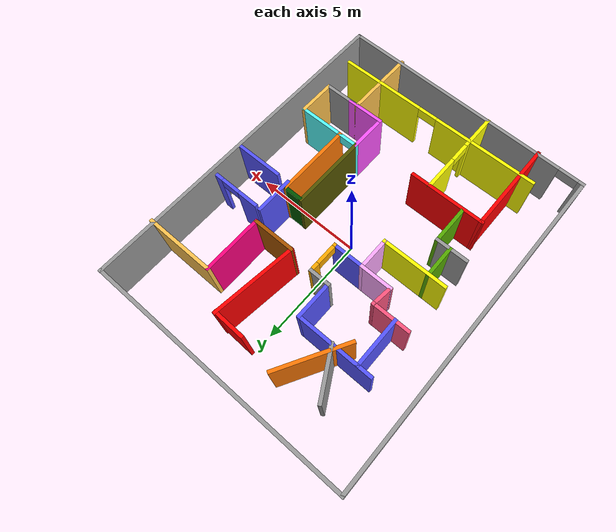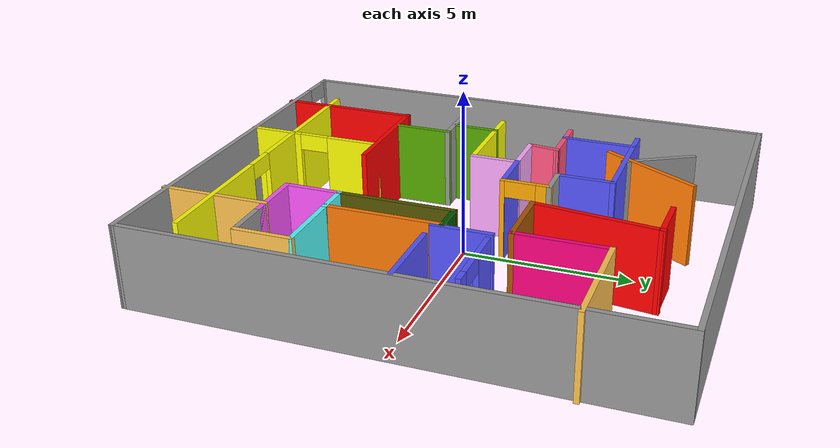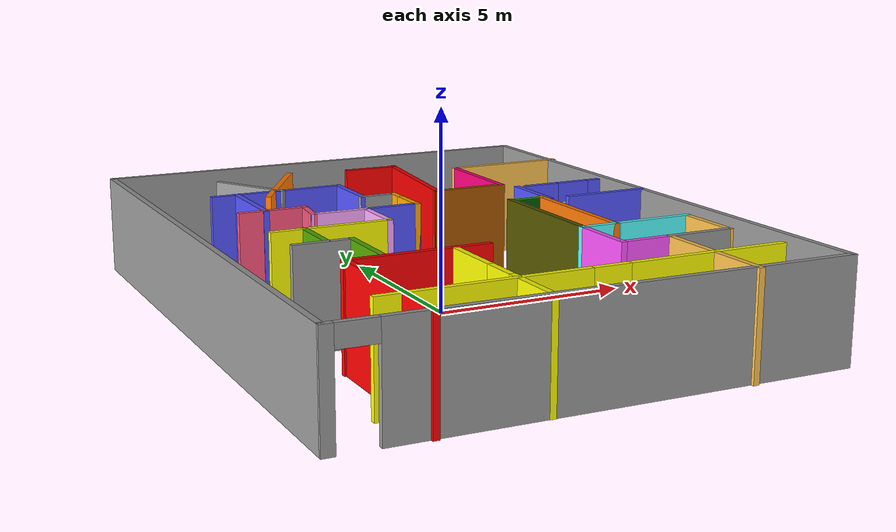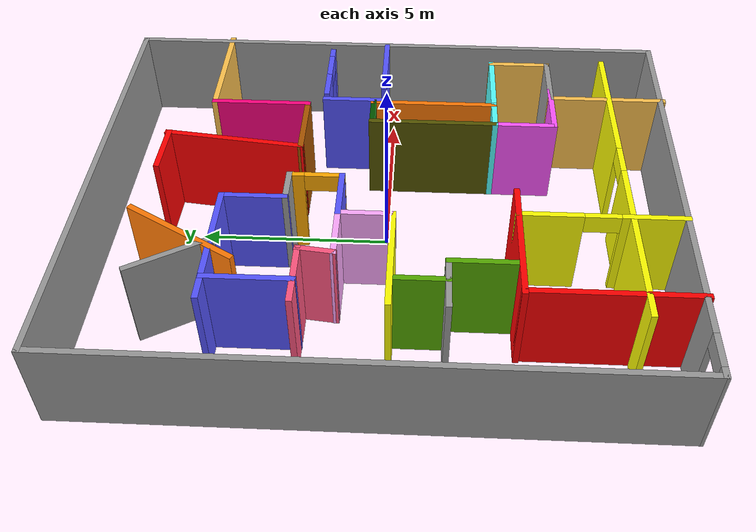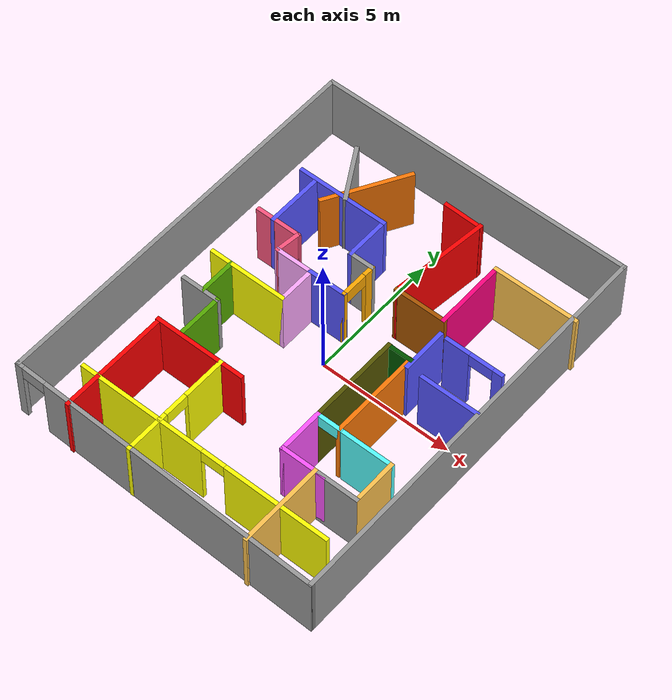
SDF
<?xml version='1.0'?>
<sdf version='1.6'>
  <model name='try_example'>
    <link name='Wall_1'>
      <pose frame=''>-5.97854 0.156676 0 0 -0 1.5708</pose>
      <self_collide>0</self_collide>
      <kinematic>0</kinematic>
      <visual name='Wall_1_Visual'>
        <pose frame=''>0 0 1.25 0 -0 0</pose>
        <geometry>
          <box>
            <size>14.9191 0.15 2.5</size>
          </box>
        </geometry>
        <material>
          <script>
            <uri>file://media/materials/scripts/gazebo.material</uri>
            <name>Gazebo/Grey</name>
          </script>
          <ambient>0 0 0 1</ambient>
          <diffuse>0.7 0.7 0.7 1</diffuse>
          <specular>0.01 0.01 0.01 1</specular>
          <emissive>0 0 0 1</emissive>
        </material>
        <cast_shadows>1</cast_shadows>
        <transparency>0</transparency>
      </visual>
      <collision name='Wall_1_Collision'>
        <laser_retro>0</laser_retro>
        <max_contacts>10</max_contacts>
        <pose frame=''>0 0 1.25 0 -0 0</pose>
        <geometry>
          <box>
            <size>14.9191 0.15 2.5</size>
          </box>
        </geometry>
        <surface>
          <friction>
            <ode>
              <mu>1</mu>
              <mu2>1</mu2>
              <fdir1>0 0 0</fdir1>
              <slip1>0</slip1>
              <slip2>0</slip2>
            </ode>
            <torsional>
              <coefficient>1</coefficient>
              <patch_radius>0</patch_radius>
              <surface_radius>0</surface_radius>
              <use_patch_radius>1</use_patch_radius>
              <ode>
                <slip>0</slip>
              </ode>
            </torsional>
          </friction>
          <bounce>
            <restitution_coefficient>0</restitution_coefficient>
            <threshold>1e+06</threshold>
          </bounce>
          <contact>
            <collide_without_contact>0</collide_without_contact>
            <collide_without_contact_bitmask>1</collide_without_contact_bitmask>
            <collide_bitmask>1</collide_bitmask>
            <ode>
              <soft_cfm>0</soft_cfm>
              <soft_erp>0.2</soft_erp>
              <kp>1e+13</kp>
              <kd>1</kd>
              <max_vel>0.01</max_vel>
              <min_depth>0</min_depth>
            </ode>
            <bullet>
              <split_impulse>1</split_impulse>
              <split_impulse_penetration_threshold>-0.01</split_impulse_penetration_threshold>
              <soft_cfm>0</soft_cfm>
              <soft_erp>0.2</soft_erp>
              <kp>1e+13</kp>
              <kd>1</kd>
            </bullet>
          </contact>
        </surface>
      </collision>
    </link>
    <link name='Wall_11'>
      <pose frame=''>4.4301 4.9191 0 0 -0 3.14159</pose>
      <self_collide>0</self_collide>
      <kinematic>0</kinematic>
      <visual name='Wall_11_Visual'>
        <pose frame=''>0 0 1.25 0 -0 0</pose>
        <geometry>
          <box>
            <size>3.25 0.15 2.5</size>
          </box>
        </geometry>
        <material>
          <script>
            <uri>file://media/materials/scripts/gazebo.material</uri>
            <name>Gazebo/Grey</name>
          </script>
          <ambient>1 0.764706 0.305882 1</ambient>
          <diffuse>0.7 0.7 0.7 1</diffuse>
          <specular>0.01 0.01 0.01 1</specular>
          <emissive>0 0 0 1</emissive>
        </material>
        <cast_shadows>1</cast_shadows>
        <transparency>0</transparency>
      </visual>
      <collision name='Wall_11_Collision'>
        <laser_retro>0</laser_retro>
        <max_contacts>10</max_contacts>
        <pose frame=''>0 0 1.25 0 -0 0</pose>
        <geometry>
          <box>
            <size>3.25 0.15 2.5</size>
          </box>
        </geometry>
        <surface>
          <friction>
            <ode>
              <mu>1</mu>
              <mu2>1</mu2>
              <fdir1>0 0 0</fdir1>
              <slip1>0</slip1>
              <slip2>0</slip2>
            </ode>
            <torsional>
              <coefficient>1</coefficient>
              <patch_radius>0</patch_radius>
              <surface_radius>0</surface_radius>
              <use_patch_radius>1</use_patch_radius>
              <ode>
                <slip>0</slip>
              </ode>
            </torsional>
          </friction>
          <bounce>
            <restitution_coefficient>0</restitution_coefficient>
            <threshold>1e+06</threshold>
          </bounce>
          <contact>
            <collide_without_contact>0</collide_without_contact>
            <collide_without_contact_bitmask>1</collide_without_contact_bitmask>
            <collide_bitmask>1</collide_bitmask>
            <ode>
              <soft_cfm>0</soft_cfm>
              <soft_erp>0.2</soft_erp>
              <kp>1e+13</kp>
              <kd>1</kd>
              <max_vel>0.01</max_vel>
              <min_depth>0</min_depth>
            </ode>
            <bullet>
              <split_impulse>1</split_impulse>
              <split_impulse_penetration_threshold>-0.01</split_impulse_penetration_threshold>
              <soft_cfm>0</soft_cfm>
              <soft_erp>0.2</soft_erp>
              <kp>1e+13</kp>
              <kd>1</kd>
            </bullet>
          </contact>
        </surface>
      </collision>
    </link>
    <link name='Wall_12'>
      <pose frame=''>2.8801 3.6191 0 0 0 -1.5708</pose>
      <self_collide>0</self_collide>
      <kinematic>0</kinematic>
      <visual name='Wall_12_Visual'>
        <pose frame=''>0 0 1.25 0 -0 0</pose>
        <geometry>
          <box>
            <size>2.75 0.15 2.5</size>
          </box>
        </geometry>
        <material>
          <script>
            <uri>file://media/materials/scripts/gazebo.material</uri>
            <name>Gazebo/Grey</name>
          </script>
          <ambient>1 0 0.498039 1</ambient>
          <diffuse>0.7 0.7 0.7 1</diffuse>
          <specular>0.01 0.01 0.01 1</specular>
          <emissive>0 0 0 1</emissive>
        </material>
        <cast_shadows>1</cast_shadows>
        <transparency>0</transparency>
      </visual>
      <collision name='Wall_12_Collision'>
        <laser_retro>0</laser_retro>
        <max_contacts>10</max_contacts>
        <pose frame=''>0 0 1.25 0 -0 0</pose>
        <geometry>
          <box>
            <size>2.75 0.15 2.5</size>
          </box>
        </geometry>
        <surface>
          <friction>
            <ode>
              <mu>1</mu>
              <mu2>1</mu2>
              <fdir1>0 0 0</fdir1>
              <slip1>0</slip1>
              <slip2>0</slip2>
            </ode>
            <torsional>
              <coefficient>1</coefficient>
              <patch_radius>0</patch_radius>
              <surface_radius>0</surface_radius>
              <use_patch_radius>1</use_patch_radius>
              <ode>
                <slip>0</slip>
              </ode>
            </torsional>
          </friction>
          <bounce>
            <restitution_coefficient>0</restitution_coefficient>
            <threshold>1e+06</threshold>
          </bounce>
          <contact>
            <collide_without_contact>0</collide_without_contact>
            <collide_without_contact_bitmask>1</collide_without_contact_bitmask>
            <collide_bitmask>1</collide_bitmask>
            <ode>
              <soft_cfm>0</soft_cfm>
              <soft_erp>0.2</soft_erp>
              <kp>1e+13</kp>
              <kd>1</kd>
              <max_vel>0.01</max_vel>
              <min_depth>0</min_depth>
            </ode>
            <bullet>
              <split_impulse>1</split_impulse>
              <split_impulse_penetration_threshold>-0.01</split_impulse_penetration_threshold>
              <soft_cfm>0</soft_cfm>
              <soft_erp>0.2</soft_erp>
              <kp>1e+13</kp>
              <kd>1</kd>
            </bullet>
          </contact>
        </surface>
      </collision>
    </link>
    <link name='Wall_13'>
      <pose frame=''>1.9551 2.3191 0 0 -0 3.14159</pose>
      <self_collide>0</self_collide>
      <kinematic>0</kinematic>
      <visual name='Wall_13_Visual'>
        <pose frame=''>0 0 1.25 0 -0 0</pose>
        <geometry>
          <box>
            <size>2 0.15 2.5</size>
          </box>
        </geometry>
        <material>
          <script>
            <uri>file://media/materials/scripts/gazebo.material</uri>
            <name>Gazebo/Grey</name>
          </script>
          <ambient>0.666667 0.333333 0 1</ambient>
          <diffuse>0.7 0.7 0.7 1</diffuse>
          <specular>0.01 0.01 0.01 1</specular>
          <emissive>0 0 0 1</emissive>
        </material>
        <cast_shadows>1</cast_shadows>
        <transparency>0</transparency>
      </visual>
      <collision name='Wall_13_Collision'>
        <laser_retro>0</laser_retro>
        <max_contacts>10</max_contacts>
        <pose frame=''>0 0 1.25 0 -0 0</pose>
        <geometry>
          <box>
            <size>2 0.15 2.5</size>
          </box>
        </geometry>
        <surface>
          <friction>
            <ode>
              <mu>1</mu>
              <mu2>1</mu2>
              <fdir1>0 0 0</fdir1>
              <slip1>0</slip1>
              <slip2>0</slip2>
            </ode>
            <torsional>
              <coefficient>1</coefficient>
              <patch_radius>0</patch_radius>
              <surface_radius>0</surface_radius>
              <use_patch_radius>1</use_patch_radius>
              <ode>
                <slip>0</slip>
              </ode>
            </torsional>
          </friction>
          <bounce>
            <restitution_coefficient>0</restitution_coefficient>
            <threshold>1e+06</threshold>
          </bounce>
          <contact>
            <collide_without_contact>0</collide_without_contact>
            <collide_without_contact_bitmask>1</collide_without_contact_bitmask>
            <collide_bitmask>1</collide_bitmask>
            <ode>
              <soft_cfm>0</soft_cfm>
              <soft_erp>0.2</soft_erp>
              <kp>1e+13</kp>
              <kd>1</kd>
              <max_vel>0.01</max_vel>
              <min_depth>0</min_depth>
            </ode>
            <bullet>
              <split_impulse>1</split_impulse>
              <split_impulse_penetration_threshold>-0.01</split_impulse_penetration_threshold>
              <soft_cfm>0</soft_cfm>
              <soft_erp>0.2</soft_erp>
              <kp>1e+13</kp>
              <kd>1</kd>
            </bullet>
          </contact>
        </surface>
      </collision>
    </link>
    <link name='Wall_14'>
      <pose frame=''>1.24117 4.12732 0 0 -0 1.45459</pose>
      <self_collide>0</self_collide>
      <kinematic>0</kinematic>
      <visual name='Wall_14_Visual'>
        <pose frame=''>0 0 1.25 0 -0 0</pose>
        <geometry>
          <box>
            <size>3.79099 0.15 2.5</size>
          </box>
        </geometry>
        <material>
          <script>
            <uri>file://media/materials/scripts/gazebo.material</uri>
            <name>Gazebo/Grey</name>
          </script>
          <ambient>1 0 0 1</ambient>
          <diffuse>0.7 0.7 0.7 1</diffuse>
          <specular>0.01 0.01 0.01 1</specular>
          <emissive>0 0 0 1</emissive>
        </material>
        <cast_shadows>1</cast_shadows>
        <transparency>0</transparency>
      </visual>
      <collision name='Wall_14_Collision'>
        <laser_retro>0</laser_retro>
        <max_contacts>10</max_contacts>
        <pose frame=''>0 0 1.25 0 -0 0</pose>
        <geometry>
          <box>
            <size>3.79099 0.15 2.5</size>
          </box>
        </geometry>
        <surface>
          <friction>
            <ode>
              <mu>1</mu>
              <mu2>1</mu2>
              <fdir1>0 0 0</fdir1>
              <slip1>0</slip1>
              <slip2>0</slip2>
            </ode>
            <torsional>
              <coefficient>1</coefficient>
              <patch_radius>0</patch_radius>
              <surface_radius>0</surface_radius>
              <use_patch_radius>1</use_patch_radius>
              <ode>
                <slip>0</slip>
              </ode>
            </torsional>
          </friction>
          <bounce>
            <restitution_coefficient>0</restitution_coefficient>
            <threshold>1e+06</threshold>
          </bounce>
          <contact>
            <collide_without_contact>0</collide_without_contact>
            <collide_without_contact_bitmask>1</collide_without_contact_bitmask>
            <collide_bitmask>1</collide_bitmask>
            <ode>
              <soft_cfm>0</soft_cfm>
              <soft_erp>0.2</soft_erp>
              <kp>1e+13</kp>
              <kd>1</kd>
              <max_vel>0.01</max_vel>
              <min_depth>0</min_depth>
            </ode>
            <bullet>
              <split_impulse>1</split_impulse>
              <split_impulse_penetration_threshold>-0.01</split_impulse_penetration_threshold>
              <soft_cfm>0</soft_cfm>
              <soft_erp>0.2</soft_erp>
              <kp>1e+13</kp>
              <kd>1</kd>
            </bullet>
          </contact>
        </surface>
      </collision>
    </link>
    <link name='Wall_15'>
      <pose frame=''>0.777248 5.91794 0 0 -0 3.11554</pose>
      <self_collide>0</self_collide>
      <kinematic>0</kinematic>
      <visual name='Wall_15_Visual'>
        <pose frame=''>0 0 1.25 0 -0 0</pose>
        <geometry>
          <box>
            <size>1.50046 0.15 2.5</size>
          </box>
        </geometry>
        <material>
          <script>
            <uri>file://media/materials/scripts/gazebo.material</uri>
            <name>Gazebo/Grey</name>
          </script>
          <ambient>1 0 0 1</ambient>
          <diffuse>0.7 0.7 0.7 1</diffuse>
          <specular>0.01 0.01 0.01 1</specular>
          <emissive>0 0 0 1</emissive>
        </material>
        <cast_shadows>1</cast_shadows>
        <transparency>0</transparency>
      </visual>
      <collision name='Wall_15_Collision'>
        <laser_retro>0</laser_retro>
        <max_contacts>10</max_contacts>
        <pose frame=''>0 0 1.25 0 -0 0</pose>
        <geometry>
          <box>
            <size>1.50046 0.15 2.5</size>
          </box>
        </geometry>
        <surface>
          <friction>
            <ode>
              <mu>1</mu>
              <mu2>1</mu2>
              <fdir1>0 0 0</fdir1>
              <slip1>0</slip1>
              <slip2>0</slip2>
            </ode>
            <torsional>
              <coefficient>1</coefficient>
              <patch_radius>0</patch_radius>
              <surface_radius>0</surface_radius>
              <use_patch_radius>1</use_patch_radius>
              <ode>
                <slip>0</slip>
              </ode>
            </torsional>
          </friction>
          <bounce>
            <restitution_coefficient>0</restitution_coefficient>
            <threshold>1e+06</threshold>
          </bounce>
          <contact>
            <collide_without_contact>0</collide_without_contact>
            <collide_without_contact_bitmask>1</collide_without_contact_bitmask>
            <collide_bitmask>1</collide_bitmask>
            <ode>
              <soft_cfm>0</soft_cfm>
              <soft_erp>0.2</soft_erp>
              <kp>1e+13</kp>
              <kd>1</kd>
              <max_vel>0.01</max_vel>
              <min_depth>0</min_depth>
            </ode>
            <bullet>
              <split_impulse>1</split_impulse>
              <split_impulse_penetration_threshold>-0.01</split_impulse_penetration_threshold>
              <soft_cfm>0</soft_cfm>
              <soft_erp>0.2</soft_erp>
              <kp>1e+13</kp>
              <kd>1</kd>
            </bullet>
          </contact>
        </surface>
      </collision>
    </link>
    <link name='Wall_17'>
      <pose frame=''>4.45382 1.83901 0 0 -0 3.14159</pose>
      <self_collide>0</self_collide>
      <kinematic>0</kinematic>
      <visual name='Wall_17_Visual_0'>
        <pose frame=''>-0.934537 0 1.25 0 -0 0</pose>
        <geometry>
          <box>
            <size>0.380925 0.15 2.5</size>
          </box>
        </geometry>
        <material>
          <script>
            <uri>file://media/materials/scripts/gazebo.material</uri>
            <name>Gazebo/Grey</name>
          </script>
          <ambient>0.333333 0.333333 1 1</ambient>
          <diffuse>0.7 0.7 0.7 1</diffuse>
          <specular>0.01 0.01 0.01 1</specular>
          <emissive>0 0 0 1</emissive>
        </material>
        <cast_shadows>1</cast_shadows>
        <transparency>0</transparency>
      </visual>
      <visual name='Wall_17_Visual_1'>
        <pose frame=''>0.640463 0 1.25 0 -0 0</pose>
        <geometry>
          <box>
            <size>0.969075 0.15 2.5</size>
          </box>
        </geometry>
        <material>
          <script>
            <uri>file://media/materials/scripts/gazebo.material</uri>
            <name>Gazebo/Grey</name>
          </script>
          <ambient>0.333333 0.333333 1 1</ambient>
          <diffuse>0.7 0.7 0.7 1</diffuse>
          <specular>0.01 0.01 0.01 1</specular>
          <emissive>0 0 0 1</emissive>
        </material>
        <cast_shadows>1</cast_shadows>
        <transparency>0</transparency>
      </visual>
      <visual name='Wall_17_Visual_2'>
        <pose frame=''>-0.294075 0 2.25 0 -0 0</pose>
        <geometry>
          <box>
            <size>0.9 0.15 0.5</size>
          </box>
        </geometry>
        <material>
          <script>
            <uri>file://media/materials/scripts/gazebo.material</uri>
            <name>Gazebo/Grey</name>
          </script>
          <ambient>0.333333 0.333333 1 1</ambient>
          <diffuse>0.7 0.7 0.7 1</diffuse>
          <specular>0.01 0.01 0.01 1</specular>
          <emissive>0 0 0 1</emissive>
        </material>
        <cast_shadows>1</cast_shadows>
        <transparency>0</transparency>
      </visual>
      <collision name='Wall_17_Collision_0'>
        <laser_retro>0</laser_retro>
        <max_contacts>10</max_contacts>
        <pose frame=''>-0.934537 0 1.25 0 -0 0</pose>
        <geometry>
          <box>
            <size>0.380925 0.15 2.5</size>
          </box>
        </geometry>
        <surface>
          <friction>
            <ode>
              <mu>1</mu>
              <mu2>1</mu2>
              <fdir1>0 0 0</fdir1>
              <slip1>0</slip1>
              <slip2>0</slip2>
            </ode>
            <torsional>
              <coefficient>1</coefficient>
              <patch_radius>0</patch_radius>
              <surface_radius>0</surface_radius>
              <use_patch_radius>1</use_patch_radius>
              <ode>
                <slip>0</slip>
              </ode>
            </torsional>
          </friction>
          <bounce>
            <restitution_coefficient>0</restitution_coefficient>
            <threshold>1e+06</threshold>
          </bounce>
          <contact>
            <collide_without_contact>0</collide_without_contact>
            <collide_without_contact_bitmask>1</collide_without_contact_bitmask>
            <collide_bitmask>1</collide_bitmask>
            <ode>
              <soft_cfm>0</soft_cfm>
              <soft_erp>0.2</soft_erp>
              <kp>1e+13</kp>
              <kd>1</kd>
              <max_vel>0.01</max_vel>
              <min_depth>0</min_depth>
            </ode>
            <bullet>
              <split_impulse>1</split_impulse>
              <split_impulse_penetration_threshold>-0.01</split_impulse_penetration_threshold>
              <soft_cfm>0</soft_cfm>
              <soft_erp>0.2</soft_erp>
              <kp>1e+13</kp>
              <kd>1</kd>
            </bullet>
          </contact>
        </surface>
      </collision>
      <collision name='Wall_17_Collision_1'>
        <laser_retro>0</laser_retro>
        <max_contacts>10</max_contacts>
        <pose frame=''>0.640463 0 1.25 0 -0 0</pose>
        <geometry>
          <box>
            <size>0.969075 0.15 2.5</size>
          </box>
        </geometry>
        <surface>
          <friction>
            <ode>
              <mu>1</mu>
              <mu2>1</mu2>
              <fdir1>0 0 0</fdir1>
              <slip1>0</slip1>
              <slip2>0</slip2>
            </ode>
            <torsional>
              <coefficient>1</coefficient>
              <patch_radius>0</patch_radius>
              <surface_radius>0</surface_radius>
              <use_patch_radius>1</use_patch_radius>
              <ode>
                <slip>0</slip>
              </ode>
            </torsional>
          </friction>
          <bounce>
            <restitution_coefficient>0</restitution_coefficient>
            <threshold>1e+06</threshold>
          </bounce>
          <contact>
            <collide_without_contact>0</collide_without_contact>
            <collide_without_contact_bitmask>1</collide_without_contact_bitmask>
            <collide_bitmask>1</collide_bitmask>
            <ode>
              <soft_cfm>0</soft_cfm>
              <soft_erp>0.2</soft_erp>
              <kp>1e+13</kp>
              <kd>1</kd>
              <max_vel>0.01</max_vel>
              <min_depth>0</min_depth>
            </ode>
            <bullet>
              <split_impulse>1</split_impulse>
              <split_impulse_penetration_threshold>-0.01</split_impulse_penetration_threshold>
              <soft_cfm>0</soft_cfm>
              <soft_erp>0.2</soft_erp>
              <kp>1e+13</kp>
              <kd>1</kd>
            </bullet>
          </contact>
        </surface>
      </collision>
      <collision name='Wall_17_Collision_2'>
        <laser_retro>0</laser_retro>
        <max_contacts>10</max_contacts>
        <pose frame=''>-0.294075 0 2.25 0 -0 0</pose>
        <geometry>
          <box>
            <size>0.9 0.15 0.5</size>
          </box>
        </geometry>
        <surface>
          <friction>
            <ode>
              <mu>1</mu>
              <mu2>1</mu2>
              <fdir1>0 0 0</fdir1>
              <slip1>0</slip1>
              <slip2>0</slip2>
            </ode>
            <torsional>
              <coefficient>1</coefficient>
              <patch_radius>0</patch_radius>
              <surface_radius>0</surface_radius>
              <use_patch_radius>1</use_patch_radius>
              <ode>
                <slip>0</slip>
              </ode>
            </torsional>
          </friction>
          <bounce>
            <restitution_coefficient>0</restitution_coefficient>
            <threshold>1e+06</threshold>
          </bounce>
          <contact>
            <collide_without_contact>0</collide_without_contact>
            <collide_without_contact_bitmask>1</collide_without_contact_bitmask>
            <collide_bitmask>1</collide_bitmask>
            <ode>
              <soft_cfm>0</soft_cfm>
              <soft_erp>0.2</soft_erp>
              <kp>1e+13</kp>
              <kd>1</kd>
              <max_vel>0.01</max_vel>
              <min_depth>0</min_depth>
            </ode>
            <bullet>
              <split_impulse>1</split_impulse>
              <split_impulse_penetration_threshold>-0.01</split_impulse_penetration_threshold>
              <soft_cfm>0</soft_cfm>
              <soft_erp>0.2</soft_erp>
              <kp>1e+13</kp>
              <kd>1</kd>
            </bullet>
          </contact>
        </surface>
      </collision>
    </link>
    <link name='Wall_18'>
      <pose frame=''>3.13064 1.04811 0 0 0 -1.5708</pose>
      <self_collide>0</self_collide>
      <kinematic>0</kinematic>
      <visual name='Wall_18_Visual'>
        <pose frame=''>0 0 1.25 0 -0 0</pose>
        <geometry>
          <box>
            <size>1.75 0.15 2.5</size>
          </box>
        </geometry>
        <material>
          <script>
            <uri>file://media/materials/scripts/gazebo.material</uri>
            <name>Gazebo/Grey</name>
          </script>
          <ambient>0.333333 0.333333 1 1</ambient>
          <diffuse>0.7 0.7 0.7 1</diffuse>
          <specular>0.01 0.01 0.01 1</specular>
          <emissive>0 0 0 1</emissive>
        </material>
        <cast_shadows>1</cast_shadows>
        <transparency>0</transparency>
      </visual>
      <collision name='Wall_18_Collision'>
        <laser_retro>0</laser_retro>
        <max_contacts>10</max_contacts>
        <pose frame=''>0 0 1.25 0 -0 0</pose>
        <geometry>
          <box>
            <size>1.75 0.15 2.5</size>
          </box>
        </geometry>
        <surface>
          <friction>
            <ode>
              <mu>1</mu>
              <mu2>1</mu2>
              <fdir1>0 0 0</fdir1>
              <slip1>0</slip1>
              <slip2>0</slip2>
            </ode>
            <torsional>
              <coefficient>1</coefficient>
              <patch_radius>0</patch_radius>
              <surface_radius>0</surface_radius>
              <use_patch_radius>1</use_patch_radius>
              <ode>
                <slip>0</slip>
              </ode>
            </torsional>
          </friction>
          <bounce>
            <restitution_coefficient>0</restitution_coefficient>
            <threshold>1e+06</threshold>
          </bounce>
          <contact>
            <collide_without_contact>0</collide_without_contact>
            <collide_without_contact_bitmask>1</collide_without_contact_bitmask>
            <collide_bitmask>1</collide_bitmask>
            <ode>
              <soft_cfm>0</soft_cfm>
              <soft_erp>0.2</soft_erp>
              <kp>1e+13</kp>
              <kd>1</kd>
              <max_vel>0.01</max_vel>
              <min_depth>0</min_depth>
            </ode>
            <bullet>
              <split_impulse>1</split_impulse>
              <split_impulse_penetration_threshold>-0.01</split_impulse_penetration_threshold>
              <soft_cfm>0</soft_cfm>
              <soft_erp>0.2</soft_erp>
              <kp>1e+13</kp>
              <kd>1</kd>
            </bullet>
          </contact>
        </surface>
      </collision>
    </link>
    <link name='Wall_24'>
      <pose frame=''>4.76828 0.244473 0 0 -0 0</pose>
      <self_collide>0</self_collide>
      <kinematic>0</kinematic>
      <visual name='Wall_24_Visual'>
        <pose frame=''>0 0 1.25 0 -0 0</pose>
        <geometry>
          <box>
            <size>2.25 0.15 2.5</size>
          </box>
        </geometry>
        <material>
          <script>
            <uri>file://media/materials/scripts/gazebo.material</uri>
            <name>Gazebo/Grey</name>
          </script>
          <ambient>0.333333 0.333333 1 1</ambient>
          <diffuse>0.7 0.7 0.7 1</diffuse>
          <specular>0.01 0.01 0.01 1</specular>
          <emissive>0 0 0 1</emissive>
        </material>
        <cast_shadows>1</cast_shadows>
        <transparency>0</transparency>
      </visual>
      <collision name='Wall_24_Collision'>
        <laser_retro>0</laser_retro>
        <max_contacts>10</max_contacts>
        <pose frame=''>0 0 1.25 0 -0 0</pose>
        <geometry>
          <box>
            <size>2.25 0.15 2.5</size>
          </box>
        </geometry>
        <surface>
          <friction>
            <ode>
              <mu>1</mu>
              <mu2>1</mu2>
              <fdir1>0 0 0</fdir1>
              <slip1>0</slip1>
              <slip2>0</slip2>
            </ode>
            <torsional>
              <coefficient>1</coefficient>
              <patch_radius>0</patch_radius>
              <surface_radius>0</surface_radius>
              <use_patch_radius>1</use_patch_radius>
              <ode>
                <slip>0</slip>
              </ode>
            </torsional>
          </friction>
          <bounce>
            <restitution_coefficient>0</restitution_coefficient>
            <threshold>1e+06</threshold>
          </bounce>
          <contact>
            <collide_without_contact>0</collide_without_contact>
            <collide_without_contact_bitmask>1</collide_without_contact_bitmask>
            <collide_bitmask>1</collide_bitmask>
            <ode>
              <soft_cfm>0</soft_cfm>
              <soft_erp>0.2</soft_erp>
              <kp>1e+13</kp>
              <kd>1</kd>
              <max_vel>0.01</max_vel>
              <min_depth>0</min_depth>
            </ode>
            <bullet>
              <split_impulse>1</split_impulse>
              <split_impulse_penetration_threshold>-0.01</split_impulse_penetration_threshold>
              <soft_cfm>0</soft_cfm>
              <soft_erp>0.2</soft_erp>
              <kp>1e+13</kp>
              <kd>1</kd>
            </bullet>
          </contact>
        </surface>
      </collision>
    </link>
    <link name='Wall_26'>
      <pose frame=''>-2.96058 -2.37202 0 0 -0 1.5708</pose>
      <self_collide>0</self_collide>
      <kinematic>0</kinematic>
      <visual name='Wall_26_Visual'>
        <pose frame=''>0 0 1.25 0 -0 0</pose>
        <geometry>
          <box>
            <size>1.75 0.15 2.5</size>
          </box>
        </geometry>
        <material>
          <script>
            <uri>file://media/materials/scripts/gazebo.material</uri>
            <name>Gazebo/Grey</name>
          </script>
          <ambient>0.333333 0.666667 0 1</ambient>
          <diffuse>0.7 0.7 0.7 1</diffuse>
          <specular>0.01 0.01 0.01 1</specular>
          <emissive>0 0 0 1</emissive>
        </material>
        <cast_shadows>1</cast_shadows>
        <transparency>0</transparency>
      </visual>
      <collision name='Wall_26_Collision'>
        <laser_retro>0</laser_retro>
        <max_contacts>10</max_contacts>
        <pose frame=''>0 0 1.25 0 -0 0</pose>
        <geometry>
          <box>
            <size>1.75 0.15 2.5</size>
          </box>
        </geometry>
        <surface>
          <friction>
            <ode>
              <mu>1</mu>
              <mu2>1</mu2>
              <fdir1>0 0 0</fdir1>
              <slip1>0</slip1>
              <slip2>0</slip2>
            </ode>
            <torsional>
              <coefficient>1</coefficient>
              <patch_radius>0</patch_radius>
              <surface_radius>0</surface_radius>
              <use_patch_radius>1</use_patch_radius>
              <ode>
                <slip>0</slip>
              </ode>
            </torsional>
          </friction>
          <bounce>
            <restitution_coefficient>0</restitution_coefficient>
            <threshold>1e+06</threshold>
          </bounce>
          <contact>
            <collide_without_contact>0</collide_without_contact>
            <collide_without_contact_bitmask>1</collide_without_contact_bitmask>
            <collide_bitmask>1</collide_bitmask>
            <ode>
              <soft_cfm>0</soft_cfm>
              <soft_erp>0.2</soft_erp>
              <kp>1e+13</kp>
              <kd>1</kd>
              <max_vel>0.01</max_vel>
              <min_depth>0</min_depth>
            </ode>
            <bullet>
              <split_impulse>1</split_impulse>
              <split_impulse_penetration_threshold>-0.01</split_impulse_penetration_threshold>
              <soft_cfm>0</soft_cfm>
              <soft_erp>0.2</soft_erp>
              <kp>1e+13</kp>
              <kd>1</kd>
            </bullet>
          </contact>
        </surface>
      </collision>
    </link>
    <link name='Wall_27'>
      <pose frame=''>-3.63558 -1.57202 0 0 -0 3.14159</pose>
      <self_collide>0</self_collide>
      <kinematic>0</kinematic>
      <visual name='Wall_27_Visual'>
        <pose frame=''>0 0 1.25 0 -0 0</pose>
        <geometry>
          <box>
            <size>1.5 0.15 2.5</size>
          </box>
        </geometry>
        <material>
          <script>
            <uri>file://media/materials/scripts/gazebo.material</uri>
            <name>Gazebo/Grey</name>
          </script>
          <ambient>1 1 1 1</ambient>
          <diffuse>0.7 0.7 0.7 1</diffuse>
          <specular>0.01 0.01 0.01 1</specular>
          <emissive>0 0 0 1</emissive>
        </material>
        <cast_shadows>1</cast_shadows>
        <transparency>0</transparency>
      </visual>
      <collision name='Wall_27_Collision'>
        <laser_retro>0</laser_retro>
        <max_contacts>10</max_contacts>
        <pose frame=''>0 0 1.25 0 -0 0</pose>
        <geometry>
          <box>
            <size>1.5 0.15 2.5</size>
          </box>
        </geometry>
        <surface>
          <friction>
            <ode>
              <mu>1</mu>
              <mu2>1</mu2>
              <fdir1>0 0 0</fdir1>
              <slip1>0</slip1>
              <slip2>0</slip2>
            </ode>
            <torsional>
              <coefficient>1</coefficient>
              <patch_radius>0</patch_radius>
              <surface_radius>0</surface_radius>
              <use_patch_radius>1</use_patch_radius>
              <ode>
                <slip>0</slip>
              </ode>
            </torsional>
          </friction>
          <bounce>
            <restitution_coefficient>0</restitution_coefficient>
            <threshold>1e+06</threshold>
          </bounce>
          <contact>
            <collide_without_contact>0</collide_without_contact>
            <collide_without_contact_bitmask>1</collide_without_contact_bitmask>
            <collide_bitmask>1</collide_bitmask>
            <ode>
              <soft_cfm>0</soft_cfm>
              <soft_erp>0.2</soft_erp>
              <kp>1e+13</kp>
              <kd>1</kd>
              <max_vel>0.01</max_vel>
              <min_depth>0</min_depth>
            </ode>
            <bullet>
              <split_impulse>1</split_impulse>
              <split_impulse_penetration_threshold>-0.01</split_impulse_penetration_threshold>
              <soft_cfm>0</soft_cfm>
              <soft_erp>0.2</soft_erp>
              <kp>1e+13</kp>
              <kd>1</kd>
            </bullet>
          </contact>
        </surface>
      </collision>
    </link>
    <link name='Wall_28'>
      <pose frame=''>-3.55189 -0.897016 0 0 -0 1.5708</pose>
      <self_collide>0</self_collide>
      <kinematic>0</kinematic>
      <visual name='Wall_28_Visual'>
        <pose frame=''>0 0 1.25 0 -0 0</pose>
        <geometry>
          <box>
            <size>1.5 0.15 2.5</size>
          </box>
        </geometry>
        <material>
          <script>
            <uri>file://media/materials/scripts/gazebo.material</uri>
            <name>Gazebo/Grey</name>
          </script>
          <ambient>0.333333 0.666667 0 1</ambient>
          <diffuse>0.7 0.7 0.7 1</diffuse>
          <specular>0.01 0.01 0.01 1</specular>
          <emissive>0 0 0 1</emissive>
        </material>
        <cast_shadows>1</cast_shadows>
        <transparency>0</transparency>
      </visual>
      <collision name='Wall_28_Collision'>
        <laser_retro>0</laser_retro>
        <max_contacts>10</max_contacts>
        <pose frame=''>0 0 1.25 0 -0 0</pose>
        <geometry>
          <box>
            <size>1.5 0.15 2.5</size>
          </box>
        </geometry>
        <surface>
          <friction>
            <ode>
              <mu>1</mu>
              <mu2>1</mu2>
              <fdir1>0 0 0</fdir1>
              <slip1>0</slip1>
              <slip2>0</slip2>
            </ode>
            <torsional>
              <coefficient>1</coefficient>
              <patch_radius>0</patch_radius>
              <surface_radius>0</surface_radius>
              <use_patch_radius>1</use_patch_radius>
              <ode>
                <slip>0</slip>
              </ode>
            </torsional>
          </friction>
          <bounce>
            <restitution_coefficient>0</restitution_coefficient>
            <threshold>1e+06</threshold>
          </bounce>
          <contact>
            <collide_without_contact>0</collide_without_contact>
            <collide_without_contact_bitmask>1</collide_without_contact_bitmask>
            <collide_bitmask>1</collide_bitmask>
            <ode>
              <soft_cfm>0</soft_cfm>
              <soft_erp>0.2</soft_erp>
              <kp>1e+13</kp>
              <kd>1</kd>
              <max_vel>0.01</max_vel>
              <min_depth>0</min_depth>
            </ode>
            <bullet>
              <split_impulse>1</split_impulse>
              <split_impulse_penetration_threshold>-0.01</split_impulse_penetration_threshold>
              <soft_cfm>0</soft_cfm>
              <soft_erp>0.2</soft_erp>
              <kp>1e+13</kp>
              <kd>1</kd>
            </bullet>
          </contact>
        </surface>
      </collision>
    </link>
    <link name='Wall_29'>
      <pose frame=''>-2.88558 -0.222018 0 0 -0 0</pose>
      <self_collide>0</self_collide>
      <kinematic>0</kinematic>
      <visual name='Wall_29_Visual'>
        <pose frame=''>0 0 1.25 0 -0 0</pose>
        <geometry>
          <box>
            <size>3 0.15 2.5</size>
          </box>
        </geometry>
        <material>
          <script>
            <uri>file://media/materials/scripts/gazebo.material</uri>
            <name>Gazebo/Grey</name>
          </script>
          <ambient>1 1 0 1</ambient>
          <diffuse>0.7 0.7 0.7 1</diffuse>
          <specular>0.01 0.01 0.01 1</specular>
          <emissive>0 0 0 1</emissive>
        </material>
        <cast_shadows>1</cast_shadows>
        <transparency>0</transparency>
      </visual>
      <collision name='Wall_29_Collision'>
        <laser_retro>0</laser_retro>
        <max_contacts>10</max_contacts>
        <pose frame=''>0 0 1.25 0 -0 0</pose>
        <geometry>
          <box>
            <size>3 0.15 2.5</size>
          </box>
        </geometry>
        <surface>
          <friction>
            <ode>
              <mu>1</mu>
              <mu2>1</mu2>
              <fdir1>0 0 0</fdir1>
              <slip1>0</slip1>
              <slip2>0</slip2>
            </ode>
            <torsional>
              <coefficient>1</coefficient>
              <patch_radius>0</patch_radius>
              <surface_radius>0</surface_radius>
              <use_patch_radius>1</use_patch_radius>
              <ode>
                <slip>0</slip>
              </ode>
            </torsional>
          </friction>
          <bounce>
            <restitution_coefficient>0</restitution_coefficient>
            <threshold>1e+06</threshold>
          </bounce>
          <contact>
            <collide_without_contact>0</collide_without_contact>
            <collide_without_contact_bitmask>1</collide_without_contact_bitmask>
            <collide_bitmask>1</collide_bitmask>
            <ode>
              <soft_cfm>0</soft_cfm>
              <soft_erp>0.2</soft_erp>
              <kp>1e+13</kp>
              <kd>1</kd>
              <max_vel>0.01</max_vel>
              <min_depth>0</min_depth>
            </ode>
            <bullet>
              <split_impulse>1</split_impulse>
              <split_impulse_penetration_threshold>-0.01</split_impulse_penetration_threshold>
              <soft_cfm>0</soft_cfm>
              <soft_erp>0.2</soft_erp>
              <kp>1e+13</kp>
              <kd>1</kd>
            </bullet>
          </contact>
        </surface>
      </collision>
    </link>
    <link name='Wall_3'>
      <pose frame=''>-0.053538 7.54122 0 0 -0 0</pose>
      <self_collide>0</self_collide>
      <kinematic>0</kinematic>
      <visual name='Wall_3_Visual'>
        <pose frame=''>0 0 1.25 0 -0 0</pose>
        <geometry>
          <box>
            <size>12 0.15 2.5</size>
          </box>
        </geometry>
        <material>
          <script>
            <uri>file://media/materials/scripts/gazebo.material</uri>
            <name>Gazebo/Grey</name>
          </script>
          <ambient>0 0 0 1</ambient>
          <diffuse>0.7 0.7 0.7 1</diffuse>
          <specular>0.01 0.01 0.01 1</specular>
          <emissive>0 0 0 1</emissive>
        </material>
        <cast_shadows>1</cast_shadows>
        <transparency>0</transparency>
      </visual>
      <collision name='Wall_3_Collision'>
        <laser_retro>0</laser_retro>
        <max_contacts>10</max_contacts>
        <pose frame=''>0 0 1.25 0 -0 0</pose>
        <geometry>
          <box>
            <size>12 0.15 2.5</size>
          </box>
        </geometry>
        <surface>
          <friction>
            <ode>
              <mu>1</mu>
              <mu2>1</mu2>
              <fdir1>0 0 0</fdir1>
              <slip1>0</slip1>
              <slip2>0</slip2>
            </ode>
            <torsional>
              <coefficient>1</coefficient>
              <patch_radius>0</patch_radius>
              <surface_radius>0</surface_radius>
              <use_patch_radius>1</use_patch_radius>
              <ode>
                <slip>0</slip>
              </ode>
            </torsional>
          </friction>
          <bounce>
            <restitution_coefficient>0</restitution_coefficient>
            <threshold>1e+06</threshold>
          </bounce>
          <contact>
            <collide_without_contact>0</collide_without_contact>
            <collide_without_contact_bitmask>1</collide_without_contact_bitmask>
            <collide_bitmask>1</collide_bitmask>
            <ode>
              <soft_cfm>0</soft_cfm>
              <soft_erp>0.2</soft_erp>
              <kp>1e+13</kp>
              <kd>1</kd>
              <max_vel>0.01</max_vel>
              <min_depth>0</min_depth>
            </ode>
            <bullet>
              <split_impulse>1</split_impulse>
              <split_impulse_penetration_threshold>-0.01</split_impulse_penetration_threshold>
              <soft_cfm>0</soft_cfm>
              <soft_erp>0.2</soft_erp>
              <kp>1e+13</kp>
              <kd>1</kd>
            </bullet>
          </contact>
        </surface>
      </collision>
    </link>
    <link name='Wall_30'>
      <pose frame=''>-1.46058 0.452981 0 0 -0 1.5708</pose>
      <self_collide>0</self_collide>
      <kinematic>0</kinematic>
      <visual name='Wall_30_Visual'>
        <pose frame=''>0 0 1.25 0 -0 0</pose>
        <geometry>
          <box>
            <size>1.5 0.15 2.5</size>
          </box>
        </geometry>
        <material>
          <script>
            <uri>file://media/materials/scripts/gazebo.material</uri>
            <name>Gazebo/Grey</name>
          </script>
          <ambient>1 0.666667 1 1</ambient>
          <diffuse>0.7 0.7 0.7 1</diffuse>
          <specular>0.01 0.01 0.01 1</specular>
          <emissive>0 0 0 1</emissive>
        </material>
        <cast_shadows>1</cast_shadows>
        <transparency>0</transparency>
      </visual>
      <collision name='Wall_30_Collision'>
        <laser_retro>0</laser_retro>
        <max_contacts>10</max_contacts>
        <pose frame=''>0 0 1.25 0 -0 0</pose>
        <geometry>
          <box>
            <size>1.5 0.15 2.5</size>
          </box>
        </geometry>
        <surface>
          <friction>
            <ode>
              <mu>1</mu>
              <mu2>1</mu2>
              <fdir1>0 0 0</fdir1>
              <slip1>0</slip1>
              <slip2>0</slip2>
            </ode>
            <torsional>
              <coefficient>1</coefficient>
              <patch_radius>0</patch_radius>
              <surface_radius>0</surface_radius>
              <use_patch_radius>1</use_patch_radius>
              <ode>
                <slip>0</slip>
              </ode>
            </torsional>
          </friction>
          <bounce>
            <restitution_coefficient>0</restitution_coefficient>
            <threshold>1e+06</threshold>
          </bounce>
          <contact>
            <collide_without_contact>0</collide_without_contact>
            <collide_without_contact_bitmask>1</collide_without_contact_bitmask>
            <collide_bitmask>1</collide_bitmask>
            <ode>
              <soft_cfm>0</soft_cfm>
              <soft_erp>0.2</soft_erp>
              <kp>1e+13</kp>
              <kd>1</kd>
              <max_vel>0.01</max_vel>
              <min_depth>0</min_depth>
            </ode>
            <bullet>
              <split_impulse>1</split_impulse>
              <split_impulse_penetration_threshold>-0.01</split_impulse_penetration_threshold>
              <soft_cfm>0</soft_cfm>
              <soft_erp>0.2</soft_erp>
              <kp>1e+13</kp>
              <kd>1</kd>
            </bullet>
          </contact>
        </surface>
      </collision>
    </link>
    <link name='Wall_31'>
      <pose frame=''>-2.13558 1.12798 0 0 -0 3.14159</pose>
      <self_collide>0</self_collide>
      <kinematic>0</kinematic>
      <visual name='Wall_31_Visual'>
        <pose frame=''>0 0 1.25 0 -0 0</pose>
        <geometry>
          <box>
            <size>1.5 0.15 2.5</size>
          </box>
        </geometry>
        <material>
          <script>
            <uri>file://media/materials/scripts/gazebo.material</uri>
            <name>Gazebo/Grey</name>
          </script>
          <ambient>1 0.666667 1 1</ambient>
          <diffuse>0.7 0.7 0.7 1</diffuse>
          <specular>0.01 0.01 0.01 1</specular>
          <emissive>0 0 0 1</emissive>
        </material>
        <cast_shadows>1</cast_shadows>
        <transparency>0</transparency>
      </visual>
      <collision name='Wall_31_Collision'>
        <laser_retro>0</laser_retro>
        <max_contacts>10</max_contacts>
        <pose frame=''>0 0 1.25 0 -0 0</pose>
        <geometry>
          <box>
            <size>1.5 0.15 2.5</size>
          </box>
        </geometry>
        <surface>
          <friction>
            <ode>
              <mu>1</mu>
              <mu2>1</mu2>
              <fdir1>0 0 0</fdir1>
              <slip1>0</slip1>
              <slip2>0</slip2>
            </ode>
            <torsional>
              <coefficient>1</coefficient>
              <patch_radius>0</patch_radius>
              <surface_radius>0</surface_radius>
              <use_patch_radius>1</use_patch_radius>
              <ode>
                <slip>0</slip>
              </ode>
            </torsional>
          </friction>
          <bounce>
            <restitution_coefficient>0</restitution_coefficient>
            <threshold>1e+06</threshold>
          </bounce>
          <contact>
            <collide_without_contact>0</collide_without_contact>
            <collide_without_contact_bitmask>1</collide_without_contact_bitmask>
            <collide_bitmask>1</collide_bitmask>
            <ode>
              <soft_cfm>0</soft_cfm>
              <soft_erp>0.2</soft_erp>
              <kp>1e+13</kp>
              <kd>1</kd>
              <max_vel>0.01</max_vel>
              <min_depth>0</min_depth>
            </ode>
            <bullet>
              <split_impulse>1</split_impulse>
              <split_impulse_penetration_threshold>-0.01</split_impulse_penetration_threshold>
              <soft_cfm>0</soft_cfm>
              <soft_erp>0.2</soft_erp>
              <kp>1e+13</kp>
              <kd>1</kd>
            </bullet>
          </contact>
        </surface>
      </collision>
    </link>
    <link name='Wall_34'>
      <pose frame=''>-0.78558 1.12798 0 0 -0 0</pose>
      <self_collide>0</self_collide>
      <kinematic>0</kinematic>
      <visual name='Wall_34_Visual'>
        <pose frame=''>0 0 1.25 0 -0 0</pose>
        <geometry>
          <box>
            <size>1.5 0.15 2.5</size>
          </box>
        </geometry>
        <material>
          <script>
            <uri>file://media/materials/scripts/gazebo.material</uri>
            <name>Gazebo/Grey</name>
          </script>
          <ambient>0.333333 0.333333 1 1</ambient>
          <diffuse>0.7 0.7 0.7 1</diffuse>
          <specular>0.01 0.01 0.01 1</specular>
          <emissive>0 0 0 1</emissive>
        </material>
        <cast_shadows>1</cast_shadows>
        <transparency>0</transparency>
      </visual>
      <collision name='Wall_34_Collision'>
        <laser_retro>0</laser_retro>
        <max_contacts>10</max_contacts>
        <pose frame=''>0 0 1.25 0 -0 0</pose>
        <geometry>
          <box>
            <size>1.5 0.15 2.5</size>
          </box>
        </geometry>
        <surface>
          <friction>
            <ode>
              <mu>1</mu>
              <mu2>1</mu2>
              <fdir1>0 0 0</fdir1>
              <slip1>0</slip1>
              <slip2>0</slip2>
            </ode>
            <torsional>
              <coefficient>1</coefficient>
              <patch_radius>0</patch_radius>
              <surface_radius>0</surface_radius>
              <use_patch_radius>1</use_patch_radius>
              <ode>
                <slip>0</slip>
              </ode>
            </torsional>
          </friction>
          <bounce>
            <restitution_coefficient>0</restitution_coefficient>
            <threshold>1e+06</threshold>
          </bounce>
          <contact>
            <collide_without_contact>0</collide_without_contact>
            <collide_without_contact_bitmask>1</collide_without_contact_bitmask>
            <collide_bitmask>1</collide_bitmask>
            <ode>
              <soft_cfm>0</soft_cfm>
              <soft_erp>0.2</soft_erp>
              <kp>1e+13</kp>
              <kd>1</kd>
              <max_vel>0.01</max_vel>
              <min_depth>0</min_depth>
            </ode>
            <bullet>
              <split_impulse>1</split_impulse>
              <split_impulse_penetration_threshold>-0.01</split_impulse_penetration_threshold>
              <soft_cfm>0</soft_cfm>
              <soft_erp>0.2</soft_erp>
              <kp>1e+13</kp>
              <kd>1</kd>
            </bullet>
          </contact>
        </surface>
      </collision>
    </link>
    <link name='Wall_35'>
      <pose frame=''>-0.11058 1.80298 0 0 -0 1.5708</pose>
      <self_collide>0</self_collide>
      <kinematic>0</kinematic>
      <visual name='Wall_35_Visual_0'>
        <pose frame=''>-0.680114 0 1.25 0 -0 0</pose>
        <geometry>
          <box>
            <size>0.139772 0.15 2.5</size>
          </box>
        </geometry>
        <material>
          <script>
            <uri>file://media/materials/scripts/gazebo.material</uri>
            <name>Gazebo/Grey</name>
          </script>
          <ambient>1 0.666667 0 1</ambient>
          <diffuse>0.7 0.7 0.7 1</diffuse>
          <specular>0.01 0.01 0.01 1</specular>
          <emissive>0 0 0 1</emissive>
        </material>
        <cast_shadows>1</cast_shadows>
        <transparency>0</transparency>
      </visual>
      <visual name='Wall_35_Visual_1'>
        <pose frame=''>0.519886 0 1.25 0 -0 0</pose>
        <geometry>
          <box>
            <size>0.460228 0.15 2.5</size>
          </box>
        </geometry>
        <material>
          <script>
            <uri>file://media/materials/scripts/gazebo.material</uri>
            <name>Gazebo/Grey</name>
          </script>
          <ambient>1 0.666667 0 1</ambient>
          <diffuse>0.7 0.7 0.7 1</diffuse>
          <specular>0.01 0.01 0.01 1</specular>
          <emissive>0 0 0 1</emissive>
        </material>
        <cast_shadows>1</cast_shadows>
        <transparency>0</transparency>
      </visual>
      <visual name='Wall_35_Visual_2'>
        <pose frame=''>-0.160228 0 2.25 0 -0 0</pose>
        <geometry>
          <box>
            <size>0.9 0.15 0.5</size>
          </box>
        </geometry>
        <material>
          <script>
            <uri>file://media/materials/scripts/gazebo.material</uri>
            <name>Gazebo/Grey</name>
          </script>
          <ambient>1 0.666667 0 1</ambient>
          <diffuse>0.7 0.7 0.7 1</diffuse>
          <specular>0.01 0.01 0.01 1</specular>
          <emissive>0 0 0 1</emissive>
        </material>
        <cast_shadows>1</cast_shadows>
        <transparency>0</transparency>
      </visual>
      <collision name='Wall_35_Collision_0'>
        <laser_retro>0</laser_retro>
        <max_contacts>10</max_contacts>
        <pose frame=''>-0.680114 0 1.25 0 -0 0</pose>
        <geometry>
          <box>
            <size>0.139772 0.15 2.5</size>
          </box>
        </geometry>
        <surface>
          <friction>
            <ode>
              <mu>1</mu>
              <mu2>1</mu2>
              <fdir1>0 0 0</fdir1>
              <slip1>0</slip1>
              <slip2>0</slip2>
            </ode>
            <torsional>
              <coefficient>1</coefficient>
              <patch_radius>0</patch_radius>
              <surface_radius>0</surface_radius>
              <use_patch_radius>1</use_patch_radius>
              <ode>
                <slip>0</slip>
              </ode>
            </torsional>
          </friction>
          <bounce>
            <restitution_coefficient>0</restitution_coefficient>
            <threshold>1e+06</threshold>
          </bounce>
          <contact>
            <collide_without_contact>0</collide_without_contact>
            <collide_without_contact_bitmask>1</collide_without_contact_bitmask>
            <collide_bitmask>1</collide_bitmask>
            <ode>
              <soft_cfm>0</soft_cfm>
              <soft_erp>0.2</soft_erp>
              <kp>1e+13</kp>
              <kd>1</kd>
              <max_vel>0.01</max_vel>
              <min_depth>0</min_depth>
            </ode>
            <bullet>
              <split_impulse>1</split_impulse>
              <split_impulse_penetration_threshold>-0.01</split_impulse_penetration_threshold>
              <soft_cfm>0</soft_cfm>
              <soft_erp>0.2</soft_erp>
              <kp>1e+13</kp>
              <kd>1</kd>
            </bullet>
          </contact>
        </surface>
      </collision>
      <collision name='Wall_35_Collision_1'>
        <laser_retro>0</laser_retro>
        <max_contacts>10</max_contacts>
        <pose frame=''>0.519886 0 1.25 0 -0 0</pose>
        <geometry>
          <box>
            <size>0.460228 0.15 2.5</size>
          </box>
        </geometry>
        <surface>
          <friction>
            <ode>
              <mu>1</mu>
              <mu2>1</mu2>
              <fdir1>0 0 0</fdir1>
              <slip1>0</slip1>
              <slip2>0</slip2>
            </ode>
            <torsional>
              <coefficient>1</coefficient>
              <patch_radius>0</patch_radius>
              <surface_radius>0</surface_radius>
              <use_patch_radius>1</use_patch_radius>
              <ode>
                <slip>0</slip>
              </ode>
            </torsional>
          </friction>
          <bounce>
            <restitution_coefficient>0</restitution_coefficient>
            <threshold>1e+06</threshold>
          </bounce>
          <contact>
            <collide_without_contact>0</collide_without_contact>
            <collide_without_contact_bitmask>1</collide_without_contact_bitmask>
            <collide_bitmask>1</collide_bitmask>
            <ode>
              <soft_cfm>0</soft_cfm>
              <soft_erp>0.2</soft_erp>
              <kp>1e+13</kp>
              <kd>1</kd>
              <max_vel>0.01</max_vel>
              <min_depth>0</min_depth>
            </ode>
            <bullet>
              <split_impulse>1</split_impulse>
              <split_impulse_penetration_threshold>-0.01</split_impulse_penetration_threshold>
              <soft_cfm>0</soft_cfm>
              <soft_erp>0.2</soft_erp>
              <kp>1e+13</kp>
              <kd>1</kd>
            </bullet>
          </contact>
        </surface>
      </collision>
      <collision name='Wall_35_Collision_2'>
        <laser_retro>0</laser_retro>
        <max_contacts>10</max_contacts>
        <pose frame=''>-0.160228 0 2.25 0 -0 0</pose>
        <geometry>
          <box>
            <size>0.9 0.15 0.5</size>
          </box>
        </geometry>
        <surface>
          <friction>
            <ode>
              <mu>1</mu>
              <mu2>1</mu2>
              <fdir1>0 0 0</fdir1>
              <slip1>0</slip1>
              <slip2>0</slip2>
            </ode>
            <torsional>
              <coefficient>1</coefficient>
              <patch_radius>0</patch_radius>
              <surface_radius>0</surface_radius>
              <use_patch_radius>1</use_patch_radius>
              <ode>
                <slip>0</slip>
              </ode>
            </torsional>
          </friction>
          <bounce>
            <restitution_coefficient>0</restitution_coefficient>
            <threshold>1e+06</threshold>
          </bounce>
          <contact>
            <collide_without_contact>0</collide_without_contact>
            <collide_without_contact_bitmask>1</collide_without_contact_bitmask>
            <collide_bitmask>1</collide_bitmask>
            <ode>
              <soft_cfm>0</soft_cfm>
              <soft_erp>0.2</soft_erp>
              <kp>1e+13</kp>
              <kd>1</kd>
              <max_vel>0.01</max_vel>
              <min_depth>0</min_depth>
            </ode>
            <bullet>
              <split_impulse>1</split_impulse>
              <split_impulse_penetration_threshold>-0.01</split_impulse_penetration_threshold>
              <soft_cfm>0</soft_cfm>
              <soft_erp>0.2</soft_erp>
              <kp>1e+13</kp>
              <kd>1</kd>
            </bullet>
          </contact>
        </surface>
      </collision>
    </link>
    <link name='Wall_36'>
      <pose frame=''>-0.53558 2.47798 0 0 -0 3.14159</pose>
      <self_collide>0</self_collide>
      <kinematic>0</kinematic>
      <visual name='Wall_36_Visual'>
        <pose frame=''>0 0 1.25 0 -0 0</pose>
        <geometry>
          <box>
            <size>1 0.15 2.5</size>
          </box>
        </geometry>
        <material>
          <script>
            <uri>file://media/materials/scripts/gazebo.material</uri>
            <name>Gazebo/Grey</name>
          </script>
          <ambient>1 1 1 1</ambient>
          <diffuse>0.7 0.7 0.7 1</diffuse>
          <specular>0.01 0.01 0.01 1</specular>
          <emissive>0 0 0 1</emissive>
        </material>
        <cast_shadows>1</cast_shadows>
        <transparency>0</transparency>
      </visual>
      <collision name='Wall_36_Collision'>
        <laser_retro>0</laser_retro>
        <max_contacts>10</max_contacts>
        <pose frame=''>0 0 1.25 0 -0 0</pose>
        <geometry>
          <box>
            <size>1 0.15 2.5</size>
          </box>
        </geometry>
        <surface>
          <friction>
            <ode>
              <mu>1</mu>
              <mu2>1</mu2>
              <fdir1>0 0 0</fdir1>
              <slip1>0</slip1>
              <slip2>0</slip2>
            </ode>
            <torsional>
              <coefficient>1</coefficient>
              <patch_radius>0</patch_radius>
              <surface_radius>0</surface_radius>
              <use_patch_radius>1</use_patch_radius>
              <ode>
                <slip>0</slip>
              </ode>
            </torsional>
          </friction>
          <bounce>
            <restitution_coefficient>0</restitution_coefficient>
            <threshold>1e+06</threshold>
          </bounce>
          <contact>
            <collide_without_contact>0</collide_without_contact>
            <collide_without_contact_bitmask>1</collide_without_contact_bitmask>
            <collide_bitmask>1</collide_bitmask>
            <ode>
              <soft_cfm>0</soft_cfm>
              <soft_erp>0.2</soft_erp>
              <kp>1e+13</kp>
              <kd>1</kd>
              <max_vel>0.01</max_vel>
              <min_depth>0</min_depth>
            </ode>
            <bullet>
              <split_impulse>1</split_impulse>
              <split_impulse_penetration_threshold>-0.01</split_impulse_penetration_threshold>
              <soft_cfm>0</soft_cfm>
              <soft_erp>0.2</soft_erp>
              <kp>1e+13</kp>
              <kd>1</kd>
            </bullet>
          </contact>
        </surface>
      </collision>
    </link>
    <link name='Wall_37'>
      <pose frame=''>-0.96058 3.27798 0 0 -0 1.5708</pose>
      <self_collide>0</self_collide>
      <kinematic>0</kinematic>
      <visual name='Wall_37_Visual'>
        <pose frame=''>0 0 1.25 0 -0 0</pose>
        <geometry>
          <box>
            <size>1.75 0.15 2.5</size>
          </box>
        </geometry>
        <material>
          <script>
            <uri>file://media/materials/scripts/gazebo.material</uri>
            <name>Gazebo/Grey</name>
          </script>
          <ambient>0.333333 0.333333 1 1</ambient>
          <diffuse>0.7 0.7 0.7 1</diffuse>
          <specular>0.01 0.01 0.01 1</specular>
          <emissive>0 0 0 1</emissive>
        </material>
        <cast_shadows>1</cast_shadows>
        <transparency>0</transparency>
      </visual>
      <collision name='Wall_37_Collision'>
        <laser_retro>0</laser_retro>
        <max_contacts>10</max_contacts>
        <pose frame=''>0 0 1.25 0 -0 0</pose>
        <geometry>
          <box>
            <size>1.75 0.15 2.5</size>
          </box>
        </geometry>
        <surface>
          <friction>
            <ode>
              <mu>1</mu>
              <mu2>1</mu2>
              <fdir1>0 0 0</fdir1>
              <slip1>0</slip1>
              <slip2>0</slip2>
            </ode>
            <torsional>
              <coefficient>1</coefficient>
              <patch_radius>0</patch_radius>
              <surface_radius>0</surface_radius>
              <use_patch_radius>1</use_patch_radius>
              <ode>
                <slip>0</slip>
              </ode>
            </torsional>
          </friction>
          <bounce>
            <restitution_coefficient>0</restitution_coefficient>
            <threshold>1e+06</threshold>
          </bounce>
          <contact>
            <collide_without_contact>0</collide_without_contact>
            <collide_without_contact_bitmask>1</collide_without_contact_bitmask>
            <collide_bitmask>1</collide_bitmask>
            <ode>
              <soft_cfm>0</soft_cfm>
              <soft_erp>0.2</soft_erp>
              <kp>1e+13</kp>
              <kd>1</kd>
              <max_vel>0.01</max_vel>
              <min_depth>0</min_depth>
            </ode>
            <bullet>
              <split_impulse>1</split_impulse>
              <split_impulse_penetration_threshold>-0.01</split_impulse_penetration_threshold>
              <soft_cfm>0</soft_cfm>
              <soft_erp>0.2</soft_erp>
              <kp>1e+13</kp>
              <kd>1</kd>
            </bullet>
          </contact>
        </surface>
      </collision>
    </link>
    <link name='Wall_38'>
      <pose frame=''>-2.63558 4.07798 0 0 -0 3.14159</pose>
      <self_collide>0</self_collide>
      <kinematic>0</kinematic>
      <visual name='Wall_38_Visual'>
        <pose frame=''>0 0 1.25 0 -0 0</pose>
        <geometry>
          <box>
            <size>3.5 0.15 2.5</size>
          </box>
        </geometry>
        <material>
          <script>
            <uri>file://media/materials/scripts/gazebo.material</uri>
            <name>Gazebo/Grey</name>
          </script>
          <ambient>0.333333 0.333333 1 1</ambient>
          <diffuse>0.7 0.7 0.7 1</diffuse>
          <specular>0.01 0.01 0.01 1</specular>
          <emissive>0 0 0 1</emissive>
        </material>
        <cast_shadows>1</cast_shadows>
        <transparency>0</transparency>
      </visual>
      <collision name='Wall_38_Collision'>
        <laser_retro>0</laser_retro>
        <max_contacts>10</max_contacts>
        <pose frame=''>0 0 1.25 0 -0 0</pose>
        <geometry>
          <box>
            <size>3.5 0.15 2.5</size>
          </box>
        </geometry>
        <surface>
          <friction>
            <ode>
              <mu>1</mu>
              <mu2>1</mu2>
              <fdir1>0 0 0</fdir1>
              <slip1>0</slip1>
              <slip2>0</slip2>
            </ode>
            <torsional>
              <coefficient>1</coefficient>
              <patch_radius>0</patch_radius>
              <surface_radius>0</surface_radius>
              <use_patch_radius>1</use_patch_radius>
              <ode>
                <slip>0</slip>
              </ode>
            </torsional>
          </friction>
          <bounce>
            <restitution_coefficient>0</restitution_coefficient>
            <threshold>1e+06</threshold>
          </bounce>
          <contact>
            <collide_without_contact>0</collide_without_contact>
            <collide_without_contact_bitmask>1</collide_without_contact_bitmask>
            <collide_bitmask>1</collide_bitmask>
            <ode>
              <soft_cfm>0</soft_cfm>
              <soft_erp>0.2</soft_erp>
              <kp>1e+13</kp>
              <kd>1</kd>
              <max_vel>0.01</max_vel>
              <min_depth>0</min_depth>
            </ode>
            <bullet>
              <split_impulse>1</split_impulse>
              <split_impulse_penetration_threshold>-0.01</split_impulse_penetration_threshold>
              <soft_cfm>0</soft_cfm>
              <soft_erp>0.2</soft_erp>
              <kp>1e+13</kp>
              <kd>1</kd>
            </bullet>
          </contact>
        </surface>
      </collision>
    </link>
    <link name='Wall_39'>
      <pose frame=''>-3.70247 3.01884 0 0 0 -1.5708</pose>
      <self_collide>0</self_collide>
      <kinematic>0</kinematic>
      <visual name='Wall_39_Visual'>
        <pose frame=''>0 0 1.25 0 -0 0</pose>
        <geometry>
          <box>
            <size>2.25 0.15 2.5</size>
          </box>
        </geometry>
        <material>
          <script>
            <uri>file://media/materials/scripts/gazebo.material</uri>
            <name>Gazebo/Grey</name>
          </script>
          <ambient>0.333333 0.333333 1 1</ambient>
          <diffuse>0.7 0.7 0.7 1</diffuse>
          <specular>0.01 0.01 0.01 1</specular>
          <emissive>0 0 0 1</emissive>
        </material>
        <cast_shadows>1</cast_shadows>
        <transparency>0</transparency>
      </visual>
      <collision name='Wall_39_Collision'>
        <laser_retro>0</laser_retro>
        <max_contacts>10</max_contacts>
        <pose frame=''>0 0 1.25 0 -0 0</pose>
        <geometry>
          <box>
            <size>2.25 0.15 2.5</size>
          </box>
        </geometry>
        <surface>
          <friction>
            <ode>
              <mu>1</mu>
              <mu2>1</mu2>
              <fdir1>0 0 0</fdir1>
              <slip1>0</slip1>
              <slip2>0</slip2>
            </ode>
            <torsional>
              <coefficient>1</coefficient>
              <patch_radius>0</patch_radius>
              <surface_radius>0</surface_radius>
              <use_patch_radius>1</use_patch_radius>
              <ode>
                <slip>0</slip>
              </ode>
            </torsional>
          </friction>
          <bounce>
            <restitution_coefficient>0</restitution_coefficient>
            <threshold>1e+06</threshold>
          </bounce>
          <contact>
            <collide_without_contact>0</collide_without_contact>
            <collide_without_contact_bitmask>1</collide_without_contact_bitmask>
            <collide_bitmask>1</collide_bitmask>
            <ode>
              <soft_cfm>0</soft_cfm>
              <soft_erp>0.2</soft_erp>
              <kp>1e+13</kp>
              <kd>1</kd>
              <max_vel>0.01</max_vel>
              <min_depth>0</min_depth>
            </ode>
            <bullet>
              <split_impulse>1</split_impulse>
              <split_impulse_penetration_threshold>-0.01</split_impulse_penetration_threshold>
              <soft_cfm>0</soft_cfm>
              <soft_erp>0.2</soft_erp>
              <kp>1e+13</kp>
              <kd>1</kd>
            </bullet>
          </contact>
        </surface>
      </collision>
    </link>
    <link name='Wall_4'>
      <pose frame=''>5.87146 0.031676 0 0 0 -1.5708</pose>
      <self_collide>0</self_collide>
      <kinematic>0</kinematic>
      <visual name='Wall_4_Visual'>
        <pose frame=''>0 0 1.25 0 -0 0</pose>
        <geometry>
          <box>
            <size>15.1691 0.15 2.5</size>
          </box>
        </geometry>
        <material>
          <script>
            <uri>file://media/materials/scripts/gazebo.material</uri>
            <name>Gazebo/Grey</name>
          </script>
          <ambient>0 0 0 1</ambient>
          <diffuse>0.7 0.7 0.7 1</diffuse>
          <specular>0.01 0.01 0.01 1</specular>
          <emissive>0 0 0 1</emissive>
        </material>
        <cast_shadows>1</cast_shadows>
        <transparency>0</transparency>
      </visual>
      <collision name='Wall_4_Collision'>
        <laser_retro>0</laser_retro>
        <max_contacts>10</max_contacts>
        <pose frame=''>0 0 1.25 0 -0 0</pose>
        <geometry>
          <box>
            <size>15.1691 0.15 2.5</size>
          </box>
        </geometry>
        <surface>
          <friction>
            <ode>
              <mu>1</mu>
              <mu2>1</mu2>
              <fdir1>0 0 0</fdir1>
              <slip1>0</slip1>
              <slip2>0</slip2>
            </ode>
            <torsional>
              <coefficient>1</coefficient>
              <patch_radius>0</patch_radius>
              <surface_radius>0</surface_radius>
              <use_patch_radius>1</use_patch_radius>
              <ode>
                <slip>0</slip>
              </ode>
            </torsional>
          </friction>
          <bounce>
            <restitution_coefficient>0</restitution_coefficient>
            <threshold>1e+06</threshold>
          </bounce>
          <contact>
            <collide_without_contact>0</collide_without_contact>
            <collide_without_contact_bitmask>1</collide_without_contact_bitmask>
            <collide_bitmask>1</collide_bitmask>
            <ode>
              <soft_cfm>0</soft_cfm>
              <soft_erp>0.2</soft_erp>
              <kp>1e+13</kp>
              <kd>1</kd>
              <max_vel>0.01</max_vel>
              <min_depth>0</min_depth>
            </ode>
            <bullet>
              <split_impulse>1</split_impulse>
              <split_impulse_penetration_threshold>-0.01</split_impulse_penetration_threshold>
              <soft_cfm>0</soft_cfm>
              <soft_erp>0.2</soft_erp>
              <kp>1e+13</kp>
              <kd>1</kd>
            </bullet>
          </contact>
        </surface>
      </collision>
    </link>
    <link name='Wall_40'>
      <pose frame=''>-3.51058 1.97798 0 0 -0 0</pose>
      <self_collide>0</self_collide>
      <kinematic>0</kinematic>
      <visual name='Wall_40_Visual'>
        <pose frame=''>0 0 1.25 0 -0 0</pose>
        <geometry>
          <box>
            <size>1.75 0.15 2.5</size>
          </box>
        </geometry>
        <material>
          <script>
            <uri>file://media/materials/scripts/gazebo.material</uri>
            <name>Gazebo/Grey</name>
          </script>
          <ambient>1 0.333333 0.498039 1</ambient>
          <diffuse>0.7 0.7 0.7 1</diffuse>
          <specular>0.01 0.01 0.01 1</specular>
          <emissive>0 0 0 1</emissive>
        </material>
        <cast_shadows>1</cast_shadows>
        <transparency>0</transparency>
      </visual>
      <collision name='Wall_40_Collision'>
        <laser_retro>0</laser_retro>
        <max_contacts>10</max_contacts>
        <pose frame=''>0 0 1.25 0 -0 0</pose>
        <geometry>
          <box>
            <size>1.75 0.15 2.5</size>
          </box>
        </geometry>
        <surface>
          <friction>
            <ode>
              <mu>1</mu>
              <mu2>1</mu2>
              <fdir1>0 0 0</fdir1>
              <slip1>0</slip1>
              <slip2>0</slip2>
            </ode>
            <torsional>
              <coefficient>1</coefficient>
              <patch_radius>0</patch_radius>
              <surface_radius>0</surface_radius>
              <use_patch_radius>1</use_patch_radius>
              <ode>
                <slip>0</slip>
              </ode>
            </torsional>
          </friction>
          <bounce>
            <restitution_coefficient>0</restitution_coefficient>
            <threshold>1e+06</threshold>
          </bounce>
          <contact>
            <collide_without_contact>0</collide_without_contact>
            <collide_without_contact_bitmask>1</collide_without_contact_bitmask>
            <collide_bitmask>1</collide_bitmask>
            <ode>
              <soft_cfm>0</soft_cfm>
              <soft_erp>0.2</soft_erp>
              <kp>1e+13</kp>
              <kd>1</kd>
              <max_vel>0.01</max_vel>
              <min_depth>0</min_depth>
            </ode>
            <bullet>
              <split_impulse>1</split_impulse>
              <split_impulse_penetration_threshold>-0.01</split_impulse_penetration_threshold>
              <soft_cfm>0</soft_cfm>
              <soft_erp>0.2</soft_erp>
              <kp>1e+13</kp>
              <kd>1</kd>
            </bullet>
          </contact>
        </surface>
      </collision>
    </link>
    <link name='Wall_44'>
      <pose frame=''>3.4314 -5.99122 0 0 -0 1.5708</pose>
      <self_collide>0</self_collide>
      <kinematic>0</kinematic>
      <visual name='Wall_44_Visual'>
        <pose frame=''>0 0 1.25 0 -0 0</pose>
        <geometry>
          <box>
            <size>3.25 0.15 2.5</size>
          </box>
        </geometry>
        <material>
          <script>
            <uri>file://media/materials/scripts/gazebo.material</uri>
            <name>Gazebo/Grey</name>
          </script>
          <ambient>1 0.764706 0.305882 1</ambient>
          <diffuse>0.7 0.7 0.7 1</diffuse>
          <specular>0.01 0.01 0.01 1</specular>
          <emissive>0 0 0 1</emissive>
        </material>
        <cast_shadows>1</cast_shadows>
        <transparency>0</transparency>
      </visual>
      <collision name='Wall_44_Collision'>
        <laser_retro>0</laser_retro>
        <max_contacts>10</max_contacts>
        <pose frame=''>0 0 1.25 0 -0 0</pose>
        <geometry>
          <box>
            <size>3.25 0.15 2.5</size>
          </box>
        </geometry>
        <surface>
          <friction>
            <ode>
              <mu>1</mu>
              <mu2>1</mu2>
              <fdir1>0 0 0</fdir1>
              <slip1>0</slip1>
              <slip2>0</slip2>
            </ode>
            <torsional>
              <coefficient>1</coefficient>
              <patch_radius>0</patch_radius>
              <surface_radius>0</surface_radius>
              <use_patch_radius>1</use_patch_radius>
              <ode>
                <slip>0</slip>
              </ode>
            </torsional>
          </friction>
          <bounce>
            <restitution_coefficient>0</restitution_coefficient>
            <threshold>1e+06</threshold>
          </bounce>
          <contact>
            <collide_without_contact>0</collide_without_contact>
            <collide_without_contact_bitmask>1</collide_without_contact_bitmask>
            <collide_bitmask>1</collide_bitmask>
            <ode>
              <soft_cfm>0</soft_cfm>
              <soft_erp>0.2</soft_erp>
              <kp>1e+13</kp>
              <kd>1</kd>
              <max_vel>0.01</max_vel>
              <min_depth>0</min_depth>
            </ode>
            <bullet>
              <split_impulse>1</split_impulse>
              <split_impulse_penetration_threshold>-0.01</split_impulse_penetration_threshold>
              <soft_cfm>0</soft_cfm>
              <soft_erp>0.2</soft_erp>
              <kp>1e+13</kp>
              <kd>1</kd>
            </bullet>
          </contact>
        </surface>
      </collision>
    </link>
    <link name='Wall_45'>
      <pose frame=''>4.2314 -4.44122 0 0 -0 0</pose>
      <self_collide>0</self_collide>
      <kinematic>0</kinematic>
      <visual name='Wall_45_Visual'>
        <pose frame=''>0 0 1.25 0 -0 0</pose>
        <geometry>
          <box>
            <size>1.75 0.15 2.5</size>
          </box>
        </geometry>
        <material>
          <script>
            <uri>file://media/materials/scripts/gazebo.material</uri>
            <name>Gazebo/Grey</name>
          </script>
          <ambient>0 0 0 1</ambient>
          <diffuse>0.7 0.7 0.7 1</diffuse>
          <specular>0.01 0.01 0.01 1</specular>
          <emissive>0 0 0 1</emissive>
        </material>
        <cast_shadows>1</cast_shadows>
        <transparency>0</transparency>
      </visual>
      <collision name='Wall_45_Collision'>
        <laser_retro>0</laser_retro>
        <max_contacts>10</max_contacts>
        <pose frame=''>0 0 1.25 0 -0 0</pose>
        <geometry>
          <box>
            <size>1.75 0.15 2.5</size>
          </box>
        </geometry>
        <surface>
          <friction>
            <ode>
              <mu>1</mu>
              <mu2>1</mu2>
              <fdir1>0 0 0</fdir1>
              <slip1>0</slip1>
              <slip2>0</slip2>
            </ode>
            <torsional>
              <coefficient>1</coefficient>
              <patch_radius>0</patch_radius>
              <surface_radius>0</surface_radius>
              <use_patch_radius>1</use_patch_radius>
              <ode>
                <slip>0</slip>
              </ode>
            </torsional>
          </friction>
          <bounce>
            <restitution_coefficient>0</restitution_coefficient>
            <threshold>1e+06</threshold>
          </bounce>
          <contact>
            <collide_without_contact>0</collide_without_contact>
            <collide_without_contact_bitmask>1</collide_without_contact_bitmask>
            <collide_bitmask>1</collide_bitmask>
            <ode>
              <soft_cfm>0</soft_cfm>
              <soft_erp>0.2</soft_erp>
              <kp>1e+13</kp>
              <kd>1</kd>
              <max_vel>0.01</max_vel>
              <min_depth>0</min_depth>
            </ode>
            <bullet>
              <split_impulse>1</split_impulse>
              <split_impulse_penetration_threshold>-0.01</split_impulse_penetration_threshold>
              <soft_cfm>0</soft_cfm>
              <soft_erp>0.2</soft_erp>
              <kp>1e+13</kp>
              <kd>1</kd>
            </bullet>
          </contact>
        </surface>
      </collision>
    </link>
    <link name='Wall_46'>
      <pose frame=''>5.0314 -3.64122 0 0 -0 1.5708</pose>
      <self_collide>0</self_collide>
      <kinematic>0</kinematic>
      <visual name='Wall_46_Visual'>
        <pose frame=''>0 0 1.25 0 -0 0</pose>
        <geometry>
          <box>
            <size>1.75 0.15 2.5</size>
          </box>
        </geometry>
        <material>
          <script>
            <uri>file://media/materials/scripts/gazebo.material</uri>
            <name>Gazebo/Grey</name>
          </script>
          <ambient>1 0.764706 0.305882 1</ambient>
          <diffuse>0.7 0.7 0.7 1</diffuse>
          <specular>0.01 0.01 0.01 1</specular>
          <emissive>0 0 0 1</emissive>
        </material>
        <cast_shadows>1</cast_shadows>
        <transparency>0</transparency>
      </visual>
      <collision name='Wall_46_Collision'>
        <laser_retro>0</laser_retro>
        <max_contacts>10</max_contacts>
        <pose frame=''>0 0 1.25 0 -0 0</pose>
        <geometry>
          <box>
            <size>1.75 0.15 2.5</size>
          </box>
        </geometry>
        <surface>
          <friction>
            <ode>
              <mu>1</mu>
              <mu2>1</mu2>
              <fdir1>0 0 0</fdir1>
              <slip1>0</slip1>
              <slip2>0</slip2>
            </ode>
            <torsional>
              <coefficient>1</coefficient>
              <patch_radius>0</patch_radius>
              <surface_radius>0</surface_radius>
              <use_patch_radius>1</use_patch_radius>
              <ode>
                <slip>0</slip>
              </ode>
            </torsional>
          </friction>
          <bounce>
            <restitution_coefficient>0</restitution_coefficient>
            <threshold>1e+06</threshold>
          </bounce>
          <contact>
            <collide_without_contact>0</collide_without_contact>
            <collide_without_contact_bitmask>1</collide_without_contact_bitmask>
            <collide_bitmask>1</collide_bitmask>
            <ode>
              <soft_cfm>0</soft_cfm>
              <soft_erp>0.2</soft_erp>
              <kp>1e+13</kp>
              <kd>1</kd>
              <max_vel>0.01</max_vel>
              <min_depth>0</min_depth>
            </ode>
            <bullet>
              <split_impulse>1</split_impulse>
              <split_impulse_penetration_threshold>-0.01</split_impulse_penetration_threshold>
              <soft_cfm>0</soft_cfm>
              <soft_erp>0.2</soft_erp>
              <kp>1e+13</kp>
              <kd>1</kd>
            </bullet>
          </contact>
        </surface>
      </collision>
    </link>
    <link name='Wall_47'>
      <pose frame=''>3.6064 -2.84122 0 0 -0 3.14159</pose>
      <self_collide>0</self_collide>
      <kinematic>0</kinematic>
      <visual name='Wall_47_Visual_0'>
        <pose frame=''>-0.515109 0 1.25 0 -0 0</pose>
        <geometry>
          <box>
            <size>1.96978 0.15 2.5</size>
          </box>
        </geometry>
        <material>
          <script>
            <uri>file://media/materials/scripts/gazebo.material</uri>
            <name>Gazebo/Grey</name>
          </script>
          <ambient>0.333333 1 1 1</ambient>
          <diffuse>0.7 0.7 0.7 1</diffuse>
          <specular>0.01 0.01 0.01 1</specular>
          <emissive>0 0 0 1</emissive>
        </material>
        <cast_shadows>1</cast_shadows>
        <transparency>0</transparency>
      </visual>
      <visual name='Wall_47_Visual_1'>
        <pose frame=''>1.43489 0 1.25 0 -0 0</pose>
        <geometry>
          <box>
            <size>0.130219 0.15 2.5</size>
          </box>
        </geometry>
        <material>
          <script>
            <uri>file://media/materials/scripts/gazebo.material</uri>
            <name>Gazebo/Grey</name>
          </script>
          <ambient>0.333333 1 1 1</ambient>
          <diffuse>0.7 0.7 0.7 1</diffuse>
          <specular>0.01 0.01 0.01 1</specular>
          <emissive>0 0 0 1</emissive>
        </material>
        <cast_shadows>1</cast_shadows>
        <transparency>0</transparency>
      </visual>
      <visual name='Wall_47_Visual_2'>
        <pose frame=''>0.919781 0 2.25 0 -0 0</pose>
        <geometry>
          <box>
            <size>0.9 0.15 0.5</size>
          </box>
        </geometry>
        <material>
          <script>
            <uri>file://media/materials/scripts/gazebo.material</uri>
            <name>Gazebo/Grey</name>
          </script>
          <ambient>0.333333 1 1 1</ambient>
          <diffuse>0.7 0.7 0.7 1</diffuse>
          <specular>0.01 0.01 0.01 1</specular>
          <emissive>0 0 0 1</emissive>
        </material>
        <cast_shadows>1</cast_shadows>
        <transparency>0</transparency>
      </visual>
      <collision name='Wall_47_Collision_0'>
        <laser_retro>0</laser_retro>
        <max_contacts>10</max_contacts>
        <pose frame=''>-0.515109 0 1.25 0 -0 0</pose>
        <geometry>
          <box>
            <size>1.96978 0.15 2.5</size>
          </box>
        </geometry>
        <surface>
          <friction>
            <ode>
              <mu>1</mu>
              <mu2>1</mu2>
              <fdir1>0 0 0</fdir1>
              <slip1>0</slip1>
              <slip2>0</slip2>
            </ode>
            <torsional>
              <coefficient>1</coefficient>
              <patch_radius>0</patch_radius>
              <surface_radius>0</surface_radius>
              <use_patch_radius>1</use_patch_radius>
              <ode>
                <slip>0</slip>
              </ode>
            </torsional>
          </friction>
          <bounce>
            <restitution_coefficient>0</restitution_coefficient>
            <threshold>1e+06</threshold>
          </bounce>
          <contact>
            <collide_without_contact>0</collide_without_contact>
            <collide_without_contact_bitmask>1</collide_without_contact_bitmask>
            <collide_bitmask>1</collide_bitmask>
            <ode>
              <soft_cfm>0</soft_cfm>
              <soft_erp>0.2</soft_erp>
              <kp>1e+13</kp>
              <kd>1</kd>
              <max_vel>0.01</max_vel>
              <min_depth>0</min_depth>
            </ode>
            <bullet>
              <split_impulse>1</split_impulse>
              <split_impulse_penetration_threshold>-0.01</split_impulse_penetration_threshold>
              <soft_cfm>0</soft_cfm>
              <soft_erp>0.2</soft_erp>
              <kp>1e+13</kp>
              <kd>1</kd>
            </bullet>
          </contact>
        </surface>
      </collision>
      <collision name='Wall_47_Collision_1'>
        <laser_retro>0</laser_retro>
        <max_contacts>10</max_contacts>
        <pose frame=''>1.43489 0 1.25 0 -0 0</pose>
        <geometry>
          <box>
            <size>0.130219 0.15 2.5</size>
          </box>
        </geometry>
        <surface>
          <friction>
            <ode>
              <mu>1</mu>
              <mu2>1</mu2>
              <fdir1>0 0 0</fdir1>
              <slip1>0</slip1>
              <slip2>0</slip2>
            </ode>
            <torsional>
              <coefficient>1</coefficient>
              <patch_radius>0</patch_radius>
              <surface_radius>0</surface_radius>
              <use_patch_radius>1</use_patch_radius>
              <ode>
                <slip>0</slip>
              </ode>
            </torsional>
          </friction>
          <bounce>
            <restitution_coefficient>0</restitution_coefficient>
            <threshold>1e+06</threshold>
          </bounce>
          <contact>
            <collide_without_contact>0</collide_without_contact>
            <collide_without_contact_bitmask>1</collide_without_contact_bitmask>
            <collide_bitmask>1</collide_bitmask>
            <ode>
              <soft_cfm>0</soft_cfm>
              <soft_erp>0.2</soft_erp>
              <kp>1e+13</kp>
              <kd>1</kd>
              <max_vel>0.01</max_vel>
              <min_depth>0</min_depth>
            </ode>
            <bullet>
              <split_impulse>1</split_impulse>
              <split_impulse_penetration_threshold>-0.01</split_impulse_penetration_threshold>
              <soft_cfm>0</soft_cfm>
              <soft_erp>0.2</soft_erp>
              <kp>1e+13</kp>
              <kd>1</kd>
            </bullet>
          </contact>
        </surface>
      </collision>
      <collision name='Wall_47_Collision_2'>
        <laser_retro>0</laser_retro>
        <max_contacts>10</max_contacts>
        <pose frame=''>0.919781 0 2.25 0 -0 0</pose>
        <geometry>
          <box>
            <size>0.9 0.15 0.5</size>
          </box>
        </geometry>
        <surface>
          <friction>
            <ode>
              <mu>1</mu>
              <mu2>1</mu2>
              <fdir1>0 0 0</fdir1>
              <slip1>0</slip1>
              <slip2>0</slip2>
            </ode>
            <torsional>
              <coefficient>1</coefficient>
              <patch_radius>0</patch_radius>
              <surface_radius>0</surface_radius>
              <use_patch_radius>1</use_patch_radius>
              <ode>
                <slip>0</slip>
              </ode>
            </torsional>
          </friction>
          <bounce>
            <restitution_coefficient>0</restitution_coefficient>
            <threshold>1e+06</threshold>
          </bounce>
          <contact>
            <collide_without_contact>0</collide_without_contact>
            <collide_without_contact_bitmask>1</collide_without_contact_bitmask>
            <collide_bitmask>1</collide_bitmask>
            <ode>
              <soft_cfm>0</soft_cfm>
              <soft_erp>0.2</soft_erp>
              <kp>1e+13</kp>
              <kd>1</kd>
              <max_vel>0.01</max_vel>
              <min_depth>0</min_depth>
            </ode>
            <bullet>
              <split_impulse>1</split_impulse>
              <split_impulse_penetration_threshold>-0.01</split_impulse_penetration_threshold>
              <soft_cfm>0</soft_cfm>
              <soft_erp>0.2</soft_erp>
              <kp>1e+13</kp>
              <kd>1</kd>
            </bullet>
          </contact>
        </surface>
      </collision>
    </link>
    <link name='Wall_48'>
      <pose frame=''>2.1814 -3.64122 0 0 0 -1.5708</pose>
      <self_collide>0</self_collide>
      <kinematic>0</kinematic>
      <visual name='Wall_48_Visual'>
        <pose frame=''>0 0 1.25 0 -0 0</pose>
        <geometry>
          <box>
            <size>1.75 0.15 2.5</size>
          </box>
        </geometry>
        <material>
          <script>
            <uri>file://media/materials/scripts/gazebo.material</uri>
            <name>Gazebo/Grey</name>
          </script>
          <ambient>1 0.333333 1 1</ambient>
          <diffuse>0.7 0.7 0.7 1</diffuse>
          <specular>0.01 0.01 0.01 1</specular>
          <emissive>0 0 0 1</emissive>
        </material>
        <cast_shadows>1</cast_shadows>
        <transparency>0</transparency>
      </visual>
      <collision name='Wall_48_Collision'>
        <laser_retro>0</laser_retro>
        <max_contacts>10</max_contacts>
        <pose frame=''>0 0 1.25 0 -0 0</pose>
        <geometry>
          <box>
            <size>1.75 0.15 2.5</size>
          </box>
        </geometry>
        <surface>
          <friction>
            <ode>
              <mu>1</mu>
              <mu2>1</mu2>
              <fdir1>0 0 0</fdir1>
              <slip1>0</slip1>
              <slip2>0</slip2>
            </ode>
            <torsional>
              <coefficient>1</coefficient>
              <patch_radius>0</patch_radius>
              <surface_radius>0</surface_radius>
              <use_patch_radius>1</use_patch_radius>
              <ode>
                <slip>0</slip>
              </ode>
            </torsional>
          </friction>
          <bounce>
            <restitution_coefficient>0</restitution_coefficient>
            <threshold>1e+06</threshold>
          </bounce>
          <contact>
            <collide_without_contact>0</collide_without_contact>
            <collide_without_contact_bitmask>1</collide_without_contact_bitmask>
            <collide_bitmask>1</collide_bitmask>
            <ode>
              <soft_cfm>0</soft_cfm>
              <soft_erp>0.2</soft_erp>
              <kp>1e+13</kp>
              <kd>1</kd>
              <max_vel>0.01</max_vel>
              <min_depth>0</min_depth>
            </ode>
            <bullet>
              <split_impulse>1</split_impulse>
              <split_impulse_penetration_threshold>-0.01</split_impulse_penetration_threshold>
              <soft_cfm>0</soft_cfm>
              <soft_erp>0.2</soft_erp>
              <kp>1e+13</kp>
              <kd>1</kd>
            </bullet>
          </contact>
        </surface>
      </collision>
    </link>
    <link name='Wall_49'>
      <pose frame=''>2.9814 -4.44122 0 0 -0 0</pose>
      <self_collide>0</self_collide>
      <kinematic>0</kinematic>
      <visual name='Wall_49_Visual'>
        <pose frame=''>0 0 1.25 0 -0 0</pose>
        <geometry>
          <box>
            <size>1.75 0.15 2.5</size>
          </box>
        </geometry>
        <material>
          <script>
            <uri>file://media/materials/scripts/gazebo.material</uri>
            <name>Gazebo/Grey</name>
          </script>
          <ambient>1 0.333333 1 1</ambient>
          <diffuse>0.7 0.7 0.7 1</diffuse>
          <specular>0.01 0.01 0.01 1</specular>
          <emissive>0 0 0 1</emissive>
        </material>
        <cast_shadows>1</cast_shadows>
        <transparency>0</transparency>
      </visual>
      <collision name='Wall_49_Collision'>
        <laser_retro>0</laser_retro>
        <max_contacts>10</max_contacts>
        <pose frame=''>0 0 1.25 0 -0 0</pose>
        <geometry>
          <box>
            <size>1.75 0.15 2.5</size>
          </box>
        </geometry>
        <surface>
          <friction>
            <ode>
              <mu>1</mu>
              <mu2>1</mu2>
              <fdir1>0 0 0</fdir1>
              <slip1>0</slip1>
              <slip2>0</slip2>
            </ode>
            <torsional>
              <coefficient>1</coefficient>
              <patch_radius>0</patch_radius>
              <surface_radius>0</surface_radius>
              <use_patch_radius>1</use_patch_radius>
              <ode>
                <slip>0</slip>
              </ode>
            </torsional>
          </friction>
          <bounce>
            <restitution_coefficient>0</restitution_coefficient>
            <threshold>1e+06</threshold>
          </bounce>
          <contact>
            <collide_without_contact>0</collide_without_contact>
            <collide_without_contact_bitmask>1</collide_without_contact_bitmask>
            <collide_bitmask>1</collide_bitmask>
            <ode>
              <soft_cfm>0</soft_cfm>
              <soft_erp>0.2</soft_erp>
              <kp>1e+13</kp>
              <kd>1</kd>
              <max_vel>0.01</max_vel>
              <min_depth>0</min_depth>
            </ode>
            <bullet>
              <split_impulse>1</split_impulse>
              <split_impulse_penetration_threshold>-0.01</split_impulse_penetration_threshold>
              <soft_cfm>0</soft_cfm>
              <soft_erp>0.2</soft_erp>
              <kp>1e+13</kp>
              <kd>1</kd>
            </bullet>
          </contact>
        </surface>
      </collision>
    </link>
    <link name='Wall_5'>
      <pose frame=''>-0.053538 -7.39332 0 0 -0 3.1205</pose>
      <self_collide>0</self_collide>
      <kinematic>0</kinematic>
      <visual name='Wall_5_Visual_0'>
        <pose frame=''>-0.600759 0 1.25 0 -0 0</pose>
        <geometry>
          <box>
            <size>10.8011 0.15 2.5</size>
          </box>
        </geometry>
        <material>
          <script>
            <uri>file://media/materials/scripts/gazebo.material</uri>
            <name>Gazebo/Grey</name>
          </script>
          <ambient>0 0 0 1</ambient>
          <diffuse>0.7 0.7 0.7 1</diffuse>
          <specular>0.01 0.01 0.01 1</specular>
          <emissive>0 0 0 1</emissive>
        </material>
        <cast_shadows>1</cast_shadows>
        <transparency>0</transparency>
      </visual>
      <visual name='Wall_5_Visual_1'>
        <pose frame=''>5.85056 0 1.25 0 -0 0</pose>
        <geometry>
          <box>
            <size>0.301518 0.15 2.5</size>
          </box>
        </geometry>
        <material>
          <script>
            <uri>file://media/materials/scripts/gazebo.material</uri>
            <name>Gazebo/Grey</name>
          </script>
          <ambient>0 0 0 1</ambient>
          <diffuse>0.7 0.7 0.7 1</diffuse>
          <specular>0.01 0.01 0.01 1</specular>
          <emissive>0 0 0 1</emissive>
        </material>
        <cast_shadows>1</cast_shadows>
        <transparency>0</transparency>
      </visual>
      <visual name='Wall_5_Visual_2'>
        <pose frame=''>5.2498 0 2.25 0 -0 0</pose>
        <geometry>
          <box>
            <size>0.9 0.15 0.5</size>
          </box>
        </geometry>
        <material>
          <script>
            <uri>file://media/materials/scripts/gazebo.material</uri>
            <name>Gazebo/Grey</name>
          </script>
          <ambient>0 0 0 1</ambient>
          <diffuse>0.7 0.7 0.7 1</diffuse>
          <specular>0.01 0.01 0.01 1</specular>
          <emissive>0 0 0 1</emissive>
        </material>
        <cast_shadows>1</cast_shadows>
        <transparency>0</transparency>
      </visual>
      <collision name='Wall_5_Collision_0'>
        <laser_retro>0</laser_retro>
        <max_contacts>10</max_contacts>
        <pose frame=''>-0.600759 0 1.25 0 -0 0</pose>
        <geometry>
          <box>
            <size>10.8011 0.15 2.5</size>
          </box>
        </geometry>
        <surface>
          <friction>
            <ode>
              <mu>1</mu>
              <mu2>1</mu2>
              <fdir1>0 0 0</fdir1>
              <slip1>0</slip1>
              <slip2>0</slip2>
            </ode>
            <torsional>
              <coefficient>1</coefficient>
              <patch_radius>0</patch_radius>
              <surface_radius>0</surface_radius>
              <use_patch_radius>1</use_patch_radius>
              <ode>
                <slip>0</slip>
              </ode>
            </torsional>
          </friction>
          <bounce>
            <restitution_coefficient>0</restitution_coefficient>
            <threshold>1e+06</threshold>
          </bounce>
          <contact>
            <collide_without_contact>0</collide_without_contact>
            <collide_without_contact_bitmask>1</collide_without_contact_bitmask>
            <collide_bitmask>1</collide_bitmask>
            <ode>
              <soft_cfm>0</soft_cfm>
              <soft_erp>0.2</soft_erp>
              <kp>1e+13</kp>
              <kd>1</kd>
              <max_vel>0.01</max_vel>
              <min_depth>0</min_depth>
            </ode>
            <bullet>
              <split_impulse>1</split_impulse>
              <split_impulse_penetration_threshold>-0.01</split_impulse_penetration_threshold>
              <soft_cfm>0</soft_cfm>
              <soft_erp>0.2</soft_erp>
              <kp>1e+13</kp>
              <kd>1</kd>
            </bullet>
          </contact>
        </surface>
      </collision>
      <collision name='Wall_5_Collision_1'>
        <laser_retro>0</laser_retro>
        <max_contacts>10</max_contacts>
        <pose frame=''>5.85056 0 1.25 0 -0 0</pose>
        <geometry>
          <box>
            <size>0.301518 0.15 2.5</size>
          </box>
        </geometry>
        <surface>
          <friction>
            <ode>
              <mu>1</mu>
              <mu2>1</mu2>
              <fdir1>0 0 0</fdir1>
              <slip1>0</slip1>
              <slip2>0</slip2>
            </ode>
            <torsional>
              <coefficient>1</coefficient>
              <patch_radius>0</patch_radius>
              <surface_radius>0</surface_radius>
              <use_patch_radius>1</use_patch_radius>
              <ode>
                <slip>0</slip>
              </ode>
            </torsional>
          </friction>
          <bounce>
            <restitution_coefficient>0</restitution_coefficient>
            <threshold>1e+06</threshold>
          </bounce>
          <contact>
            <collide_without_contact>0</collide_without_contact>
            <collide_without_contact_bitmask>1</collide_without_contact_bitmask>
            <collide_bitmask>1</collide_bitmask>
            <ode>
              <soft_cfm>0</soft_cfm>
              <soft_erp>0.2</soft_erp>
              <kp>1e+13</kp>
              <kd>1</kd>
              <max_vel>0.01</max_vel>
              <min_depth>0</min_depth>
            </ode>
            <bullet>
              <split_impulse>1</split_impulse>
              <split_impulse_penetration_threshold>-0.01</split_impulse_penetration_threshold>
              <soft_cfm>0</soft_cfm>
              <soft_erp>0.2</soft_erp>
              <kp>1e+13</kp>
              <kd>1</kd>
            </bullet>
          </contact>
        </surface>
      </collision>
      <collision name='Wall_5_Collision_2'>
        <laser_retro>0</laser_retro>
        <max_contacts>10</max_contacts>
        <pose frame=''>5.2498 0 2.25 0 -0 0</pose>
        <geometry>
          <box>
            <size>0.9 0.15 0.5</size>
          </box>
        </geometry>
        <surface>
          <friction>
            <ode>
              <mu>1</mu>
              <mu2>1</mu2>
              <fdir1>0 0 0</fdir1>
              <slip1>0</slip1>
              <slip2>0</slip2>
            </ode>
            <torsional>
              <coefficient>1</coefficient>
              <patch_radius>0</patch_radius>
              <surface_radius>0</surface_radius>
              <use_patch_radius>1</use_patch_radius>
              <ode>
                <slip>0</slip>
              </ode>
            </torsional>
          </friction>
          <bounce>
            <restitution_coefficient>0</restitution_coefficient>
            <threshold>1e+06</threshold>
          </bounce>
          <contact>
            <collide_without_contact>0</collide_without_contact>
            <collide_without_contact_bitmask>1</collide_without_contact_bitmask>
            <collide_bitmask>1</collide_bitmask>
            <ode>
              <soft_cfm>0</soft_cfm>
              <soft_erp>0.2</soft_erp>
              <kp>1e+13</kp>
              <kd>1</kd>
              <max_vel>0.01</max_vel>
              <min_depth>0</min_depth>
            </ode>
            <bullet>
              <split_impulse>1</split_impulse>
              <split_impulse_penetration_threshold>-0.01</split_impulse_penetration_threshold>
              <soft_cfm>0</soft_cfm>
              <soft_erp>0.2</soft_erp>
              <kp>1e+13</kp>
              <kd>1</kd>
            </bullet>
          </contact>
        </surface>
      </collision>
    </link>
    <link name='Wall_51'>
      <pose frame=''>0.406817 -6.05023 0 0 -0 0</pose>
      <self_collide>0</self_collide>
      <kinematic>0</kinematic>
      <visual name='Wall_51_Visual_1'>
        <pose frame=''>2.88516 0 1.25 0 -0 0</pose>
        <geometry>
          <box>
            <size>3.97968 0.15 2.5</size>
          </box>
        </geometry>
        <material>
          <script>
            <uri>file://media/materials/scripts/gazebo.material</uri>
            <name>Gazebo/Grey</name>
          </script>
          <ambient>1 1 0 1</ambient>
          <diffuse>0.7 0.7 0.7 1</diffuse>
          <specular>0.01 0.01 0.01 1</specular>
          <emissive>0 0 0 1</emissive>
        </material>
        <cast_shadows>1</cast_shadows>
        <transparency>0</transparency>
      </visual>
      <visual name='Wall_51_Visual_0'>
        <pose frame=''>-2.43984 0 1.25 0 -0 0</pose>
        <geometry>
          <box>
            <size>4.87032 0.15 2.5</size>
          </box>
        </geometry>
        <material>
          <script>
            <uri>file://media/materials/scripts/gazebo.material</uri>
            <name>Gazebo/Grey</name>
          </script>
          <ambient>1 1 0 1</ambient>
          <diffuse>0.7 0.7 0.7 1</diffuse>
          <specular>0.01 0.01 0.01 1</specular>
          <emissive>0 0 0 1</emissive>
        </material>
        <cast_shadows>1</cast_shadows>
        <transparency>0</transparency>
      </visual>
      <visual name='Wall_51_Visual_2'>
        <pose frame=''>0.445322 0 2.25 0 -0 0</pose>
        <geometry>
          <box>
            <size>0.9 0.15 0.5</size>
          </box>
        </geometry>
        <material>
          <script>
            <uri>file://media/materials/scripts/gazebo.material</uri>
            <name>Gazebo/Grey</name>
          </script>
          <ambient>1 1 0 1</ambient>
          <diffuse>0.7 0.7 0.7 1</diffuse>
          <specular>0.01 0.01 0.01 1</specular>
          <emissive>0 0 0 1</emissive>
        </material>
        <cast_shadows>1</cast_shadows>
        <transparency>0</transparency>
      </visual>
      <collision name='Wall_51_Collision_0'>
        <laser_retro>0</laser_retro>
        <max_contacts>10</max_contacts>
        <pose frame=''>-2.43984 0 1.25 0 -0 0</pose>
        <geometry>
          <box>
            <size>4.87032 0.15 2.5</size>
          </box>
        </geometry>
        <surface>
          <friction>
            <ode>
              <mu>1</mu>
              <mu2>1</mu2>
              <fdir1>0 0 0</fdir1>
              <slip1>0</slip1>
              <slip2>0</slip2>
            </ode>
            <torsional>
              <coefficient>1</coefficient>
              <patch_radius>0</patch_radius>
              <surface_radius>0</surface_radius>
              <use_patch_radius>1</use_patch_radius>
              <ode>
                <slip>0</slip>
              </ode>
            </torsional>
          </friction>
          <bounce>
            <restitution_coefficient>0</restitution_coefficient>
            <threshold>1e+06</threshold>
          </bounce>
          <contact>
            <collide_without_contact>0</collide_without_contact>
            <collide_without_contact_bitmask>1</collide_without_contact_bitmask>
            <collide_bitmask>1</collide_bitmask>
            <ode>
              <soft_cfm>0</soft_cfm>
              <soft_erp>0.2</soft_erp>
              <kp>1e+13</kp>
              <kd>1</kd>
              <max_vel>0.01</max_vel>
              <min_depth>0</min_depth>
            </ode>
            <bullet>
              <split_impulse>1</split_impulse>
              <split_impulse_penetration_threshold>-0.01</split_impulse_penetration_threshold>
              <soft_cfm>0</soft_cfm>
              <soft_erp>0.2</soft_erp>
              <kp>1e+13</kp>
              <kd>1</kd>
            </bullet>
          </contact>
        </surface>
      </collision>
      <collision name='Wall_51_Collision_1'>
        <laser_retro>0</laser_retro>
        <max_contacts>10</max_contacts>
        <pose frame=''>2.88516 0 1.25 0 -0 0</pose>
        <geometry>
          <box>
            <size>3.97968 0.15 2.5</size>
          </box>
        </geometry>
        <surface>
          <friction>
            <ode>
              <mu>1</mu>
              <mu2>1</mu2>
              <fdir1>0 0 0</fdir1>
              <slip1>0</slip1>
              <slip2>0</slip2>
            </ode>
            <torsional>
              <coefficient>1</coefficient>
              <patch_radius>0</patch_radius>
              <surface_radius>0</surface_radius>
              <use_patch_radius>1</use_patch_radius>
              <ode>
                <slip>0</slip>
              </ode>
            </torsional>
          </friction>
          <bounce>
            <restitution_coefficient>0</restitution_coefficient>
            <threshold>1e+06</threshold>
          </bounce>
          <contact>
            <collide_without_contact>0</collide_without_contact>
            <collide_without_contact_bitmask>1</collide_without_contact_bitmask>
            <collide_bitmask>1</collide_bitmask>
            <ode>
              <soft_cfm>0</soft_cfm>
              <soft_erp>0.2</soft_erp>
              <kp>1e+13</kp>
              <kd>1</kd>
              <max_vel>0.01</max_vel>
              <min_depth>0</min_depth>
            </ode>
            <bullet>
              <split_impulse>1</split_impulse>
              <split_impulse_penetration_threshold>-0.01</split_impulse_penetration_threshold>
              <soft_cfm>0</soft_cfm>
              <soft_erp>0.2</soft_erp>
              <kp>1e+13</kp>
              <kd>1</kd>
            </bullet>
          </contact>
        </surface>
      </collision>
      <collision name='Wall_51_Collision_2'>
        <laser_retro>0</laser_retro>
        <max_contacts>10</max_contacts>
        <pose frame=''>0.445322 0 2.25 0 -0 0</pose>
        <geometry>
          <box>
            <size>0.9 0.15 0.5</size>
          </box>
        </geometry>
        <surface>
          <friction>
            <ode>
              <mu>1</mu>
              <mu2>1</mu2>
              <fdir1>0 0 0</fdir1>
              <slip1>0</slip1>
              <slip2>0</slip2>
            </ode>
            <torsional>
              <coefficient>1</coefficient>
              <patch_radius>0</patch_radius>
              <surface_radius>0</surface_radius>
              <use_patch_radius>1</use_patch_radius>
              <ode>
                <slip>0</slip>
              </ode>
            </torsional>
          </friction>
          <bounce>
            <restitution_coefficient>0</restitution_coefficient>
            <threshold>1e+06</threshold>
          </bounce>
          <contact>
            <collide_without_contact>0</collide_without_contact>
            <collide_without_contact_bitmask>1</collide_without_contact_bitmask>
            <collide_bitmask>1</collide_bitmask>
            <ode>
              <soft_cfm>0</soft_cfm>
              <soft_erp>0.2</soft_erp>
              <kp>1e+13</kp>
              <kd>1</kd>
              <max_vel>0.01</max_vel>
              <min_depth>0</min_depth>
            </ode>
            <bullet>
              <split_impulse>1</split_impulse>
              <split_impulse_penetration_threshold>-0.01</split_impulse_penetration_threshold>
              <soft_cfm>0</soft_cfm>
              <soft_erp>0.2</soft_erp>
              <kp>1e+13</kp>
              <kd>1</kd>
            </bullet>
          </contact>
        </surface>
      </collision>
    </link>
    <link name='Wall_53'>
      <pose frame=''>-2.76058 1.55298 0 0 0 -1.6879</pose>
      <self_collide>0</self_collide>
      <kinematic>0</kinematic>
      <visual name='Wall_53_Visual'>
        <pose frame=''>0 0 1.25 0 -0 0</pose>
        <geometry>
          <box>
            <size>1.00586 0.15 2.5</size>
          </box>
        </geometry>
        <material>
          <script>
            <uri>file://media/materials/scripts/gazebo.material</uri>
            <name>Gazebo/Grey</name>
          </script>
          <ambient>1 0.333333 0.498039 1</ambient>
          <diffuse>0.7 0.7 0.7 1</diffuse>
          <specular>0.01 0.01 0.01 1</specular>
          <emissive>0 0 0 1</emissive>
        </material>
        <cast_shadows>1</cast_shadows>
        <transparency>0</transparency>
      </visual>
      <collision name='Wall_53_Collision'>
        <laser_retro>0</laser_retro>
        <max_contacts>10</max_contacts>
        <pose frame=''>0 0 1.25 0 -0 0</pose>
        <geometry>
          <box>
            <size>1.00586 0.15 2.5</size>
          </box>
        </geometry>
        <surface>
          <friction>
            <ode>
              <mu>1</mu>
              <mu2>1</mu2>
              <fdir1>0 0 0</fdir1>
              <slip1>0</slip1>
              <slip2>0</slip2>
            </ode>
            <torsional>
              <coefficient>1</coefficient>
              <patch_radius>0</patch_radius>
              <surface_radius>0</surface_radius>
              <use_patch_radius>1</use_patch_radius>
              <ode>
                <slip>0</slip>
              </ode>
            </torsional>
          </friction>
          <bounce>
            <restitution_coefficient>0</restitution_coefficient>
            <threshold>1e+06</threshold>
          </bounce>
          <contact>
            <collide_without_contact>0</collide_without_contact>
            <collide_without_contact_bitmask>1</collide_without_contact_bitmask>
            <collide_bitmask>1</collide_bitmask>
            <ode>
              <soft_cfm>0</soft_cfm>
              <soft_erp>0.2</soft_erp>
              <kp>1e+13</kp>
              <kd>1</kd>
              <max_vel>0.01</max_vel>
              <min_depth>0</min_depth>
            </ode>
            <bullet>
              <split_impulse>1</split_impulse>
              <split_impulse_penetration_threshold>-0.01</split_impulse_penetration_threshold>
              <soft_cfm>0</soft_cfm>
              <soft_erp>0.2</soft_erp>
              <kp>1e+13</kp>
              <kd>1</kd>
            </bullet>
          </contact>
        </surface>
      </collision>
    </link>
    <link name='Wall_55'>
      <pose frame=''>2.1814 -1.16622 0 0 -0 1.5708</pose>
      <self_collide>0</self_collide>
      <kinematic>0</kinematic>
      <visual name='Wall_55_Visual'>
        <pose frame=''>0 0 1.25 0 -0 0</pose>
        <geometry>
          <box>
            <size>3.5 0.15 2.5</size>
          </box>
        </geometry>
        <material>
          <script>
            <uri>file://media/materials/scripts/gazebo.material</uri>
            <name>Gazebo/Grey</name>
          </script>
          <ambient>0.333333 0.333333 0 1</ambient>
          <diffuse>0.7 0.7 0.7 1</diffuse>
          <specular>0.01 0.01 0.01 1</specular>
          <emissive>0 0 0 1</emissive>
        </material>
        <cast_shadows>1</cast_shadows>
        <transparency>0</transparency>
      </visual>
      <collision name='Wall_55_Collision'>
        <laser_retro>0</laser_retro>
        <max_contacts>10</max_contacts>
        <pose frame=''>0 0 1.25 0 -0 0</pose>
        <geometry>
          <box>
            <size>3.5 0.15 2.5</size>
          </box>
        </geometry>
        <surface>
          <friction>
            <ode>
              <mu>1</mu>
              <mu2>1</mu2>
              <fdir1>0 0 0</fdir1>
              <slip1>0</slip1>
              <slip2>0</slip2>
            </ode>
            <torsional>
              <coefficient>1</coefficient>
              <patch_radius>0</patch_radius>
              <surface_radius>0</surface_radius>
              <use_patch_radius>1</use_patch_radius>
              <ode>
                <slip>0</slip>
              </ode>
            </torsional>
          </friction>
          <bounce>
            <restitution_coefficient>0</restitution_coefficient>
            <threshold>1e+06</threshold>
          </bounce>
          <contact>
            <collide_without_contact>0</collide_without_contact>
            <collide_without_contact_bitmask>1</collide_without_contact_bitmask>
            <collide_bitmask>1</collide_bitmask>
            <ode>
              <soft_cfm>0</soft_cfm>
              <soft_erp>0.2</soft_erp>
              <kp>1e+13</kp>
              <kd>1</kd>
              <max_vel>0.01</max_vel>
              <min_depth>0</min_depth>
            </ode>
            <bullet>
              <split_impulse>1</split_impulse>
              <split_impulse_penetration_threshold>-0.01</split_impulse_penetration_threshold>
              <soft_cfm>0</soft_cfm>
              <soft_erp>0.2</soft_erp>
              <kp>1e+13</kp>
              <kd>1</kd>
            </bullet>
          </contact>
        </surface>
      </collision>
    </link>
    <link name='Wall_56'>
      <pose frame=''>2.62687 0.495726 0 0 -0 0</pose>
      <self_collide>0</self_collide>
      <kinematic>0</kinematic>
      <visual name='Wall_56_Visual'>
        <pose frame=''>0 0 1.25 0 -0 0</pose>
        <geometry>
          <box>
            <size>1 0.15 2.5</size>
          </box>
        </geometry>
        <material>
          <script>
            <uri>file://media/materials/scripts/gazebo.material</uri>
            <name>Gazebo/Grey</name>
          </script>
          <ambient>0 0.333333 0 1</ambient>
          <diffuse>0.7 0.7 0.7 1</diffuse>
          <specular>0.01 0.01 0.01 1</specular>
          <emissive>0 0 0 1</emissive>
        </material>
        <cast_shadows>1</cast_shadows>
        <transparency>0</transparency>
      </visual>
      <collision name='Wall_56_Collision'>
        <laser_retro>0</laser_retro>
        <max_contacts>10</max_contacts>
        <pose frame=''>0 0 1.25 0 -0 0</pose>
        <geometry>
          <box>
            <size>1 0.15 2.5</size>
          </box>
        </geometry>
        <surface>
          <friction>
            <ode>
              <mu>1</mu>
              <mu2>1</mu2>
              <fdir1>0 0 0</fdir1>
              <slip1>0</slip1>
              <slip2>0</slip2>
            </ode>
            <torsional>
              <coefficient>1</coefficient>
              <patch_radius>0</patch_radius>
              <surface_radius>0</surface_radius>
              <use_patch_radius>1</use_patch_radius>
              <ode>
                <slip>0</slip>
              </ode>
            </torsional>
          </friction>
          <bounce>
            <restitution_coefficient>0</restitution_coefficient>
            <threshold>1e+06</threshold>
          </bounce>
          <contact>
            <collide_without_contact>0</collide_without_contact>
            <collide_without_contact_bitmask>1</collide_without_contact_bitmask>
            <collide_bitmask>1</collide_bitmask>
            <ode>
              <soft_cfm>0</soft_cfm>
              <soft_erp>0.2</soft_erp>
              <kp>1e+13</kp>
              <kd>1</kd>
              <max_vel>0.01</max_vel>
              <min_depth>0</min_depth>
            </ode>
            <bullet>
              <split_impulse>1</split_impulse>
              <split_impulse_penetration_threshold>-0.01</split_impulse_penetration_threshold>
              <soft_cfm>0</soft_cfm>
              <soft_erp>0.2</soft_erp>
              <kp>1e+13</kp>
              <kd>1</kd>
            </bullet>
          </contact>
        </surface>
      </collision>
    </link>
    <link name='Wall_57'>
      <pose frame=''>3.0314 -1.16622 0 0 0 -1.5708</pose>
      <self_collide>0</self_collide>
      <kinematic>0</kinematic>
      <visual name='Wall_57_Visual'>
        <pose frame=''>0 0 1.25 0 -0 0</pose>
        <geometry>
          <box>
            <size>3.5 0.15 2.5</size>
          </box>
        </geometry>
        <material>
          <script>
            <uri>file://media/materials/scripts/gazebo.material</uri>
            <name>Gazebo/Grey</name>
          </script>
          <ambient>0.996078 0.47451 0.0196078 1</ambient>
          <diffuse>0.7 0.7 0.7 1</diffuse>
          <specular>0.01 0.01 0.01 1</specular>
          <emissive>0 0 0 1</emissive>
        </material>
        <cast_shadows>1</cast_shadows>
        <transparency>0</transparency>
      </visual>
      <collision name='Wall_57_Collision'>
        <laser_retro>0</laser_retro>
        <max_contacts>10</max_contacts>
        <pose frame=''>0 0 1.25 0 -0 0</pose>
        <geometry>
          <box>
            <size>3.5 0.15 2.5</size>
          </box>
        </geometry>
        <surface>
          <friction>
            <ode>
              <mu>1</mu>
              <mu2>1</mu2>
              <fdir1>0 0 0</fdir1>
              <slip1>0</slip1>
              <slip2>0</slip2>
            </ode>
            <torsional>
              <coefficient>1</coefficient>
              <patch_radius>0</patch_radius>
              <surface_radius>0</surface_radius>
              <use_patch_radius>1</use_patch_radius>
              <ode>
                <slip>0</slip>
              </ode>
            </torsional>
          </friction>
          <bounce>
            <restitution_coefficient>0</restitution_coefficient>
            <threshold>1e+06</threshold>
          </bounce>
          <contact>
            <collide_without_contact>0</collide_without_contact>
            <collide_without_contact_bitmask>1</collide_without_contact_bitmask>
            <collide_bitmask>1</collide_bitmask>
            <ode>
              <soft_cfm>0</soft_cfm>
              <soft_erp>0.2</soft_erp>
              <kp>1e+13</kp>
              <kd>1</kd>
              <max_vel>0.01</max_vel>
              <min_depth>0</min_depth>
            </ode>
            <bullet>
              <split_impulse>1</split_impulse>
              <split_impulse_penetration_threshold>-0.01</split_impulse_penetration_threshold>
              <soft_cfm>0</soft_cfm>
              <soft_erp>0.2</soft_erp>
              <kp>1e+13</kp>
              <kd>1</kd>
            </bullet>
          </contact>
        </surface>
      </collision>
    </link>
    <link name='Wall_67'>
      <pose frame=''>-3.0359 4.97057 0 0 -0 2.0944</pose>
      <self_collide>0</self_collide>
      <kinematic>0</kinematic>
      <visual name='Wall_67_Visual'>
        <pose frame=''>0 0 1.25 0 -0 0</pose>
        <geometry>
          <box>
            <size>2.25 0.15 2.5</size>
          </box>
        </geometry>
        <material>
          <script>
            <uri>file://media/materials/scripts/gazebo.material</uri>
            <name>Gazebo/Grey</name>
          </script>
          <ambient>1 1 1 1</ambient>
          <diffuse>0.7 0.7 0.7 1</diffuse>
          <specular>0.01 0.01 0.01 1</specular>
          <emissive>0 0 0 1</emissive>
        </material>
        <cast_shadows>1</cast_shadows>
        <transparency>0</transparency>
      </visual>
      <collision name='Wall_67_Collision'>
        <laser_retro>0</laser_retro>
        <max_contacts>10</max_contacts>
        <pose frame=''>0 0 1.25 0 -0 0</pose>
        <geometry>
          <box>
            <size>2.25 0.15 2.5</size>
          </box>
        </geometry>
        <surface>
          <friction>
            <ode>
              <mu>1</mu>
              <mu2>1</mu2>
              <fdir1>0 0 0</fdir1>
              <slip1>0</slip1>
              <slip2>0</slip2>
            </ode>
            <torsional>
              <coefficient>1</coefficient>
              <patch_radius>0</patch_radius>
              <surface_radius>0</surface_radius>
              <use_patch_radius>1</use_patch_radius>
              <ode>
                <slip>0</slip>
              </ode>
            </torsional>
          </friction>
          <bounce>
            <restitution_coefficient>0</restitution_coefficient>
            <threshold>1e+06</threshold>
          </bounce>
          <contact>
            <collide_without_contact>0</collide_without_contact>
            <collide_without_contact_bitmask>1</collide_without_contact_bitmask>
            <collide_bitmask>1</collide_bitmask>
            <ode>
              <soft_cfm>0</soft_cfm>
              <soft_erp>0.2</soft_erp>
              <kp>1e+13</kp>
              <kd>1</kd>
              <max_vel>0.01</max_vel>
              <min_depth>0</min_depth>
            </ode>
            <bullet>
              <split_impulse>1</split_impulse>
              <split_impulse_penetration_threshold>-0.01</split_impulse_penetration_threshold>
              <soft_cfm>0</soft_cfm>
              <soft_erp>0.2</soft_erp>
              <kp>1e+13</kp>
              <kd>1</kd>
            </bullet>
          </contact>
        </surface>
      </collision>
    </link>
    <link name='Wall_69'>
      <pose frame=''>-2.29021 4.86314 0 0 -0 1.0472</pose>
      <self_collide>0</self_collide>
      <kinematic>0</kinematic>
      <visual name='Wall_69_Visual'>
        <pose frame=''>0 0 1.25 0 -0 0</pose>
        <geometry>
          <box>
            <size>3.25 0.15 2.5</size>
          </box>
        </geometry>
        <material>
          <script>
            <uri>file://media/materials/scripts/gazebo.material</uri>
            <name>Gazebo/Grey</name>
          </script>
          <ambient>0.996078 0.47451 0.0196078 1</ambient>
          <diffuse>0.7 0.7 0.7 1</diffuse>
          <specular>0.01 0.01 0.01 1</specular>
          <emissive>0 0 0 1</emissive>
        </material>
        <cast_shadows>1</cast_shadows>
        <transparency>0</transparency>
      </visual>
      <collision name='Wall_69_Collision'>
        <laser_retro>0</laser_retro>
        <max_contacts>10</max_contacts>
        <pose frame=''>0 0 1.25 0 -0 0</pose>
        <geometry>
          <box>
            <size>3.25 0.15 2.5</size>
          </box>
        </geometry>
        <surface>
          <friction>
            <ode>
              <mu>1</mu>
              <mu2>1</mu2>
              <fdir1>0 0 0</fdir1>
              <slip1>0</slip1>
              <slip2>0</slip2>
            </ode>
            <torsional>
              <coefficient>1</coefficient>
              <patch_radius>0</patch_radius>
              <surface_radius>0</surface_radius>
              <use_patch_radius>1</use_patch_radius>
              <ode>
                <slip>0</slip>
              </ode>
            </torsional>
          </friction>
          <bounce>
            <restitution_coefficient>0</restitution_coefficient>
            <threshold>1e+06</threshold>
          </bounce>
          <contact>
            <collide_without_contact>0</collide_without_contact>
            <collide_without_contact_bitmask>1</collide_without_contact_bitmask>
            <collide_bitmask>1</collide_bitmask>
            <ode>
              <soft_cfm>0</soft_cfm>
              <soft_erp>0.2</soft_erp>
              <kp>1e+13</kp>
              <kd>1</kd>
              <max_vel>0.01</max_vel>
              <min_depth>0</min_depth>
            </ode>
            <bullet>
              <split_impulse>1</split_impulse>
              <split_impulse_penetration_threshold>-0.01</split_impulse_penetration_threshold>
              <soft_cfm>0</soft_cfm>
              <soft_erp>0.2</soft_erp>
              <kp>1e+13</kp>
              <kd>1</kd>
            </bullet>
          </contact>
        </surface>
      </collision>
    </link>
    <link name='Wall_7'>
      <pose frame=''>-3.8025 -5.3294 0 0 -0 1.5708</pose>
      <self_collide>0</self_collide>
      <kinematic>0</kinematic>
      <visual name='Wall_7_Visual'>
        <pose frame=''>0 0 1.25 0 -0 0</pose>
        <geometry>
          <box>
            <size>4.25 0.15 2.5</size>
          </box>
        </geometry>
        <material>
          <script>
            <uri>file://media/materials/scripts/gazebo.material</uri>
            <name>Gazebo/Grey</name>
          </script>
          <ambient>1 0 0 1</ambient>
          <diffuse>0.7 0.7 0.7 1</diffuse>
          <specular>0.01 0.01 0.01 1</specular>
          <emissive>0 0 0 1</emissive>
        </material>
        <cast_shadows>1</cast_shadows>
        <transparency>0</transparency>
      </visual>
      <collision name='Wall_7_Collision'>
        <laser_retro>0</laser_retro>
        <max_contacts>10</max_contacts>
        <pose frame=''>0 0 1.25 0 -0 0</pose>
        <geometry>
          <box>
            <size>4.25 0.15 2.5</size>
          </box>
        </geometry>
        <surface>
          <friction>
            <ode>
              <mu>1</mu>
              <mu2>1</mu2>
              <fdir1>0 0 0</fdir1>
              <slip1>0</slip1>
              <slip2>0</slip2>
            </ode>
            <torsional>
              <coefficient>1</coefficient>
              <patch_radius>0</patch_radius>
              <surface_radius>0</surface_radius>
              <use_patch_radius>1</use_patch_radius>
              <ode>
                <slip>0</slip>
              </ode>
            </torsional>
          </friction>
          <bounce>
            <restitution_coefficient>0</restitution_coefficient>
            <threshold>1e+06</threshold>
          </bounce>
          <contact>
            <collide_without_contact>0</collide_without_contact>
            <collide_without_contact_bitmask>1</collide_without_contact_bitmask>
            <collide_bitmask>1</collide_bitmask>
            <ode>
              <soft_cfm>0</soft_cfm>
              <soft_erp>0.2</soft_erp>
              <kp>1e+13</kp>
              <kd>1</kd>
              <max_vel>0.01</max_vel>
              <min_depth>0</min_depth>
            </ode>
            <bullet>
              <split_impulse>1</split_impulse>
              <split_impulse_penetration_threshold>-0.01</split_impulse_penetration_threshold>
              <soft_cfm>0</soft_cfm>
              <soft_erp>0.2</soft_erp>
              <kp>1e+13</kp>
              <kd>1</kd>
            </bullet>
          </contact>
        </surface>
      </collision>
    </link>
    <link name='Wall_8'>
      <pose frame=''>-2.16977 -3.2794 0 0 -0 0</pose>
      <self_collide>0</self_collide>
      <kinematic>0</kinematic>
      <visual name='Wall_8_Visual'>
        <pose frame=''>0 0 1.25 0 -0 0</pose>
        <geometry>
          <box>
            <size>3.5 0.15 2.5</size>
          </box>
        </geometry>
        <material>
          <script>
            <uri>file://media/materials/scripts/gazebo.material</uri>
            <name>Gazebo/Grey</name>
          </script>
          <ambient>1 0 0 1</ambient>
          <diffuse>0.7 0.7 0.7 1</diffuse>
          <specular>0.01 0.01 0.01 1</specular>
          <emissive>0 0 0 1</emissive>
        </material>
        <cast_shadows>1</cast_shadows>
        <transparency>0</transparency>
      </visual>
      <collision name='Wall_8_Collision'>
        <laser_retro>0</laser_retro>
        <max_contacts>10</max_contacts>
        <pose frame=''>0 0 1.25 0 -0 0</pose>
        <geometry>
          <box>
            <size>3.5 0.15 2.5</size>
          </box>
        </geometry>
        <surface>
          <friction>
            <ode>
              <mu>1</mu>
              <mu2>1</mu2>
              <fdir1>0 0 0</fdir1>
              <slip1>0</slip1>
              <slip2>0</slip2>
            </ode>
            <torsional>
              <coefficient>1</coefficient>
              <patch_radius>0</patch_radius>
              <surface_radius>0</surface_radius>
              <use_patch_radius>1</use_patch_radius>
              <ode>
                <slip>0</slip>
              </ode>
            </torsional>
          </friction>
          <bounce>
            <restitution_coefficient>0</restitution_coefficient>
            <threshold>1e+06</threshold>
          </bounce>
          <contact>
            <collide_without_contact>0</collide_without_contact>
            <collide_without_contact_bitmask>1</collide_without_contact_bitmask>
            <collide_bitmask>1</collide_bitmask>
            <ode>
              <soft_cfm>0</soft_cfm>
              <soft_erp>0.2</soft_erp>
              <kp>1e+13</kp>
              <kd>1</kd>
              <max_vel>0.01</max_vel>
              <min_depth>0</min_depth>
            </ode>
            <bullet>
              <split_impulse>1</split_impulse>
              <split_impulse_penetration_threshold>-0.01</split_impulse_penetration_threshold>
              <soft_cfm>0</soft_cfm>
              <soft_erp>0.2</soft_erp>
              <kp>1e+13</kp>
              <kd>1</kd>
            </bullet>
          </contact>
        </surface>
      </collision>
    </link>
    <link name='Wall_9'>
      <pose frame=''>-1.30971 -5.3294 0 0 0 -1.5708</pose>
      <self_collide>0</self_collide>
      <kinematic>0</kinematic>
      <visual name='Wall_9_Visual_0'>
        <pose frame=''>-1.28932 0 1.25 0 -0 0</pose>
        <geometry>
          <box>
            <size>1.67136 0.15 2.5</size>
          </box>
        </geometry>
        <material>
          <script>
            <uri>file://media/materials/scripts/gazebo.material</uri>
            <name>Gazebo/Grey</name>
          </script>
          <ambient>1 1 0 1</ambient>
          <diffuse>0.7 0.7 0.7 1</diffuse>
          <specular>0.01 0.01 0.01 1</specular>
          <emissive>0 0 0 1</emissive>
        </material>
        <cast_shadows>1</cast_shadows>
        <transparency>0</transparency>
      </visual>
      <visual name='Wall_9_Visual_1'>
        <pose frame=''>1.28568 0 1.25 0 -0 0</pose>
        <geometry>
          <box>
            <size>1.67864 0.15 2.5</size>
          </box>
        </geometry>
        <material>
          <script>
            <uri>file://media/materials/scripts/gazebo.material</uri>
            <name>Gazebo/Grey</name>
          </script>
          <ambient>1 1 0 1</ambient>
          <diffuse>0.7 0.7 0.7 1</diffuse>
          <specular>0.01 0.01 0.01 1</specular>
          <emissive>0 0 0 1</emissive>
        </material>
        <cast_shadows>1</cast_shadows>
        <transparency>0</transparency>
      </visual>
      <visual name='Wall_9_Visual_2'>
        <pose frame=''>-0.003643 0 2.25 0 -0 0</pose>
        <geometry>
          <box>
            <size>0.9 0.15 0.5</size>
          </box>
        </geometry>
        <material>
          <script>
            <uri>file://media/materials/scripts/gazebo.material</uri>
            <name>Gazebo/Grey</name>
          </script>
          <ambient>1 1 0 1</ambient>
          <diffuse>0.7 0.7 0.7 1</diffuse>
          <specular>0.01 0.01 0.01 1</specular>
          <emissive>0 0 0 1</emissive>
        </material>
        <cast_shadows>1</cast_shadows>
        <transparency>0</transparency>
      </visual>
      <collision name='Wall_9_Collision_0'>
        <laser_retro>0</laser_retro>
        <max_contacts>10</max_contacts>
        <pose frame=''>-1.28932 0 1.25 0 -0 0</pose>
        <geometry>
          <box>
            <size>1.67136 0.15 2.5</size>
          </box>
        </geometry>
        <surface>
          <friction>
            <ode>
              <mu>1</mu>
              <mu2>1</mu2>
              <fdir1>0 0 0</fdir1>
              <slip1>0</slip1>
              <slip2>0</slip2>
            </ode>
            <torsional>
              <coefficient>1</coefficient>
              <patch_radius>0</patch_radius>
              <surface_radius>0</surface_radius>
              <use_patch_radius>1</use_patch_radius>
              <ode>
                <slip>0</slip>
              </ode>
            </torsional>
          </friction>
          <bounce>
            <restitution_coefficient>0</restitution_coefficient>
            <threshold>1e+06</threshold>
          </bounce>
          <contact>
            <collide_without_contact>0</collide_without_contact>
            <collide_without_contact_bitmask>1</collide_without_contact_bitmask>
            <collide_bitmask>1</collide_bitmask>
            <ode>
              <soft_cfm>0</soft_cfm>
              <soft_erp>0.2</soft_erp>
              <kp>1e+13</kp>
              <kd>1</kd>
              <max_vel>0.01</max_vel>
              <min_depth>0</min_depth>
            </ode>
            <bullet>
              <split_impulse>1</split_impulse>
              <split_impulse_penetration_threshold>-0.01</split_impulse_penetration_threshold>
              <soft_cfm>0</soft_cfm>
              <soft_erp>0.2</soft_erp>
              <kp>1e+13</kp>
              <kd>1</kd>
            </bullet>
          </contact>
        </surface>
      </collision>
      <collision name='Wall_9_Collision_1'>
        <laser_retro>0</laser_retro>
        <max_contacts>10</max_contacts>
        <pose frame=''>1.28568 0 1.25 0 -0 0</pose>
        <geometry>
          <box>
            <size>1.67864 0.15 2.5</size>
          </box>
        </geometry>
        <surface>
          <friction>
            <ode>
              <mu>1</mu>
              <mu2>1</mu2>
              <fdir1>0 0 0</fdir1>
              <slip1>0</slip1>
              <slip2>0</slip2>
            </ode>
            <torsional>
              <coefficient>1</coefficient>
              <patch_radius>0</patch_radius>
              <surface_radius>0</surface_radius>
              <use_patch_radius>1</use_patch_radius>
              <ode>
                <slip>0</slip>
              </ode>
            </torsional>
          </friction>
          <bounce>
            <restitution_coefficient>0</restitution_coefficient>
            <threshold>1e+06</threshold>
          </bounce>
          <contact>
            <collide_without_contact>0</collide_without_contact>
            <collide_without_contact_bitmask>1</collide_without_contact_bitmask>
            <collide_bitmask>1</collide_bitmask>
            <ode>
              <soft_cfm>0</soft_cfm>
              <soft_erp>0.2</soft_erp>
              <kp>1e+13</kp>
              <kd>1</kd>
              <max_vel>0.01</max_vel>
              <min_depth>0</min_depth>
            </ode>
            <bullet>
              <split_impulse>1</split_impulse>
              <split_impulse_penetration_threshold>-0.01</split_impulse_penetration_threshold>
              <soft_cfm>0</soft_cfm>
              <soft_erp>0.2</soft_erp>
              <kp>1e+13</kp>
              <kd>1</kd>
            </bullet>
          </contact>
        </surface>
      </collision>
      <collision name='Wall_9_Collision_2'>
        <laser_retro>0</laser_retro>
        <max_contacts>10</max_contacts>
        <pose frame=''>-0.003643 0 2.25 0 -0 0</pose>
        <geometry>
          <box>
            <size>0.9 0.15 0.5</size>
          </box>
        </geometry>
        <surface>
          <friction>
            <ode>
              <mu>1</mu>
              <mu2>1</mu2>
              <fdir1>0 0 0</fdir1>
              <slip1>0</slip1>
              <slip2>0</slip2>
            </ode>
            <torsional>
              <coefficient>1</coefficient>
              <patch_radius>0</patch_radius>
              <surface_radius>0</surface_radius>
              <use_patch_radius>1</use_patch_radius>
              <ode>
                <slip>0</slip>
              </ode>
            </torsional>
          </friction>
          <bounce>
            <restitution_coefficient>0</restitution_coefficient>
            <threshold>1e+06</threshold>
          </bounce>
          <contact>
            <collide_without_contact>0</collide_without_contact>
            <collide_without_contact_bitmask>1</collide_without_contact_bitmask>
            <collide_bitmask>1</collide_bitmask>
            <ode>
              <soft_cfm>0</soft_cfm>
              <soft_erp>0.2</soft_erp>
              <kp>1e+13</kp>
              <kd>1</kd>
              <max_vel>0.01</max_vel>
              <min_depth>0</min_depth>
            </ode>
            <bullet>
              <split_impulse>1</split_impulse>
              <split_impulse_penetration_threshold>-0.01</split_impulse_penetration_threshold>
              <soft_cfm>0</soft_cfm>
              <soft_erp>0.2</soft_erp>
              <kp>1e+13</kp>
              <kd>1</kd>
            </bullet>
          </contact>
        </surface>
      </collision>
    </link>
    <static>1</static>
    <allow_auto_disable>1</allow_auto_disable>
  </model>
</sdf>
